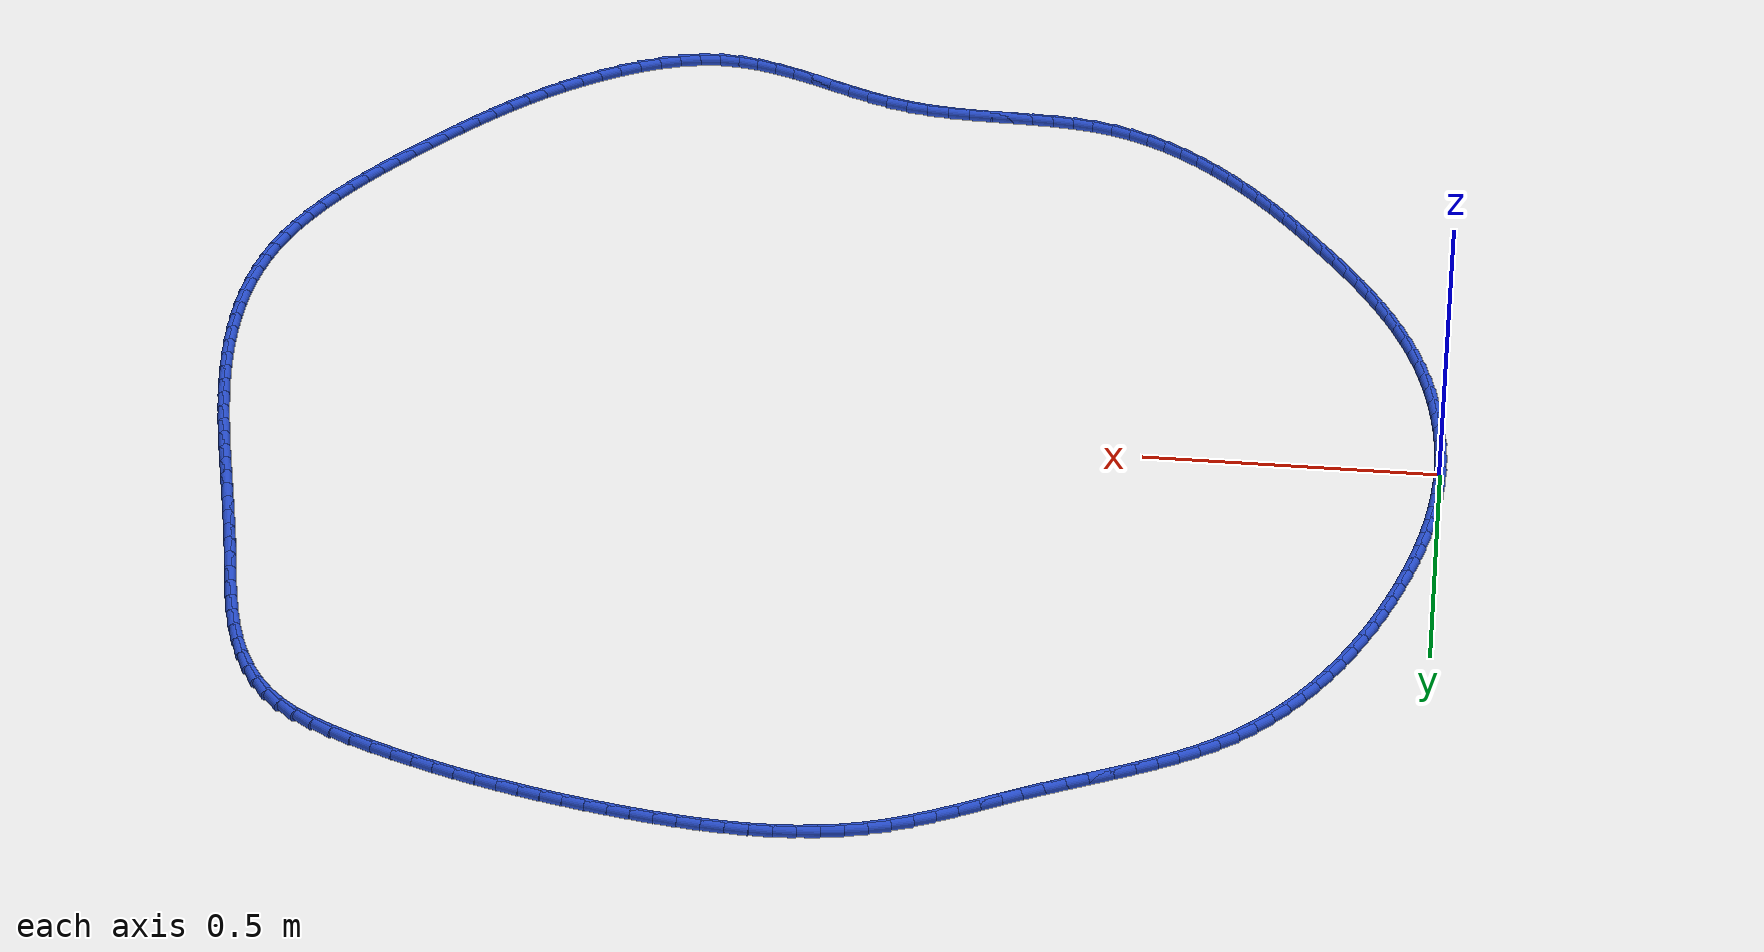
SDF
<sdf version="1.6">
 <world name="default">
  <light name="sun" type="directional">
   <pose>0 0 10 0 -0 0</pose>
   <diffuse>0.8 0.8 0.8 1</diffuse>
   <specular>0.2 0.2 0.2 1</specular>
   <attenuation>
    <range>1000</range>
    <constant>0.9</constant>
    <linear>0.01</linear>
    <quadratic>0.001</quadratic>
   </attenuation>
   <direction>-0.5 0.1 -0.9</direction>
  </light>
  <model name="ground_plane">
   <static>1</static>
   <link name="link">
    <collision name="collision">
     <geometry><plane><normal>0 0 1</normal><size>100 100</size></plane></geometry>
     <surface><friction><ode><mu>100</mu><mu2>50</mu2></ode></friction></surface>
    </collision>
    <visual name="visual">
     <cast_shadows>0</cast_shadows>
     <geometry><plane><normal>0 0 1</normal><size>100 100</size></plane></geometry>
     <material>
      <script><uri>file://media/materials/scripts/gazebo.material</uri><name>Gazebo/WhiteGlow</name></script>
     </material>
    </visual>
   </link>
  </model>
  <gravity>0 0 -9.8</gravity>
  <magnetic_field>6e-06 2.3e-05 -4.2e-05</magnetic_field>
  <atmosphere type="adiabatic"/>
  <physics name="default_physics" default="0" type="ode">
   <max_step_size>0.001</max_step_size>
   <real_time_factor>1</real_time_factor>
   <real_time_update_rate>1000</real_time_update_rate>
  </physics>
  <scene><ambient>0.4 0.4 0.4 1</ambient><background>0.7 0.7 0.7 1</background><shadows>1</shadows></scene>
  <spherical_coordinates>
   <surface_model>EARTH_WGS84</surface_model>
   <latitude_deg>0</latitude_deg>
   <longitude_deg>0</longitude_deg>
   <elevation>0</elevation>
   <heading_deg>0</heading_deg>
  </spherical_coordinates>
  <model name="line">
   <link name="link_0">
    <pose>-2.7755575615628914e-17 -9.71445146547012e-17 0.01 0 1.57 1.542044267432709</pose>
    <collision name="collision">
     <geometry><cylinder><radius>0.01</radius><length>0.08</length></cylinder></geometry>
    </collision>
    <visual name="visual">
     <material>
      <script><name>Gazebo/Blue</name><uri>file://media/materials/scripts/gazebo.material</uri></script>
     </material>
     <geometry><cylinder><radius>0.01</radius><length>0.08</length></cylinder></geometry>
    </visual>
   </link>
   <link name="link_1">
    <pose>0.0010738321835704202 0.03733771721228712 0.01 0 1.57 1.5032818511181816</pose>
    <collision name="collision">
     <geometry><cylinder><radius>0.01</radius><length>0.08</length></cylinder></geometry>
    </collision>
    <visual name="visual">
     <material>
      <script><name>Gazebo/Blue</name><uri>file://media/materials/scripts/gazebo.material</uri></script>
     </material>
     <geometry><cylinder><radius>0.01</radius><length>0.08</length></cylinder></geometry>
    </visual>
   </link>
   <link name="link_2">
    <pose>0.0035869679635209934 0.07450480074108565 0.01 0 1.57 1.4658785739195797</pose>
    <collision name="collision">
     <geometry><cylinder><radius>0.01</radius><length>0.08</length></cylinder></geometry>
    </collision>
    <visual name="visual">
     <material>
      <script><name>Gazebo/Blue</name><uri>file://media/materials/scripts/gazebo.material</uri></script>
     </material>
     <geometry><cylinder><radius>0.01</radius><length>0.08</length></cylinder></geometry>
    </visual>
   </link>
   <link name="link_3">
    <pose>0.007484704561177816 0.11151878774079305 0.01 0 1.57 1.4299813160270398</pose>
    <collision name="collision">
     <geometry><cylinder><radius>0.01</radius><length>0.08</length></cylinder></geometry>
    </collision>
    <visual name="visual">
     <material>
      <script><name>Gazebo/Blue</name><uri>file://media/materials/scripts/gazebo.material</uri></script>
     </material>
     <geometry><cylinder><radius>0.01</radius><length>0.08</length></cylinder></geometry>
    </visual>
   </link>
   <link name="link_4">
    <pose>0.012712339197867031 0.14839721536580708 0.01 0 1.57 1.39570997917218</pose>
    <collision name="collision">
     <geometry><cylinder><radius>0.01</radius><length>0.08</length></cylinder></geometry>
    </collision>
    <visual name="visual">
     <material>
      <script><name>Gazebo/Blue</name><uri>file://media/materials/scripts/gazebo.material</uri></script>
     </material>
     <geometry><cylinder><radius>0.01</radius><length>0.08</length></cylinder></geometry>
    </visual>
   </link>
   <link name="link_5">
    <pose>0.01921516909491475 0.18515762077052528 0.01 0 1.57 1.3631578961786874</pose>
    <collision name="collision">
     <geometry><cylinder><radius>0.01</radius><length>0.08</length></cylinder></geometry>
    </collision>
    <visual name="visual">
     <material>
      <script><name>Gazebo/Blue</name><uri>file://media/materials/scripts/gazebo.material</uri></script>
     </material>
     <geometry><cylinder><radius>0.01</radius><length>0.08</length></cylinder></geometry>
    </visual>
   </link>
   <link name="link_6">
    <pose>0.026938491473647123 0.22181754110934537 0.01 0 1.57 1.332393237809248</pose>
    <collision name="collision">
     <geometry><cylinder><radius>0.01</radius><length>0.08</length></cylinder></geometry>
    </collision>
    <visual name="visual">
     <material>
      <script><name>Gazebo/Blue</name><uri>file://media/materials/scripts/gazebo.material</uri></script>
     </material>
     <geometry><cylinder><radius>0.01</radius><length>0.08</length></cylinder></geometry>
    </visual>
   </link>
   <link name="link_7">
    <pose>0.035827603555390275 0.2583945135366649 0.01 0 1.57 1.3034611595035999</pose>
    <collision name="collision">
     <geometry><cylinder><radius>0.01</radius><length>0.08</length></cylinder></geometry>
    </collision>
    <visual name="visual">
     <material>
      <script><name>Gazebo/Blue</name><uri>file://media/materials/scripts/gazebo.material</uri></script>
     </material>
     <geometry><cylinder><radius>0.01</radius><length>0.08</length></cylinder></geometry>
    </visual>
   </link>
   <link name="link_8">
    <pose>0.04582780256147033 0.29490607520688167 0.01 0 1.57 1.2763864294501093</pose>
    <collision name="collision">
     <geometry><cylinder><radius>0.01</radius><length>0.08</length></cylinder></geometry>
    </collision>
    <visual name="visual">
     <material>
      <script><name>Gazebo/Blue</name><uri>file://media/materials/scripts/gazebo.material</uri></script>
     </material>
     <geometry><cylinder><radius>0.01</radius><length>0.08</length></cylinder></geometry>
    </visual>
   </link>
   <link name="link_9">
    <pose>0.056884385713213415 0.3313697632743931 0.01 0 1.57 1.250950686429554</pose>
    <collision name="collision">
     <geometry><cylinder><radius>0.01</radius><length>0.08</length></cylinder></geometry>
    </collision>
    <visual name="visual">
     <material>
      <script><name>Gazebo/Blue</name><uri>file://media/materials/scripts/gazebo.material</uri></script>
     </material>
     <geometry><cylinder><radius>0.01</radius><length>0.08</length></cylinder></geometry>
    </visual>
   </link>
   <link name="link_10">
    <pose>0.06894845416542092 0.36779309989886144 0.01 0 1.57 1.2248352163170741</pose>
    <collision name="collision">
     <geometry><cylinder><radius>0.01</radius><length>0.08</length></cylinder></geometry>
    </collision>
    <visual name="visual">
     <material>
      <script><name>Gazebo/Blue</name><uri>file://media/materials/scripts/gazebo.material</uri></script>
     </material>
     <geometry><cylinder><radius>0.01</radius><length>0.08</length></cylinder></geometry>
    </visual>
   </link>
   <link name="link_11">
    <pose>0.08202943260990407 0.4040829668865384 0.01 0 1.57 1.1965557212852407</pose>
    <collision name="collision">
     <geometry><cylinder><radius>0.01</radius><length>0.08</length></cylinder></geometry>
    </collision>
    <visual name="visual">
     <material>
      <script><name>Gazebo/Blue</name><uri>file://media/materials/scripts/gazebo.material</uri></script>
     </material>
     <geometry><cylinder><radius>0.01</radius><length>0.08</length></cylinder></geometry>
    </visual>
   </link>
   <link name="link_12">
    <pose>0.0961704415835236 0.4400881020776531 0.01 0 1.57 1.1658818972682463</pose>
    <collision name="collision">
     <geometry><cylinder><radius>0.01</radius><length>0.08</length></cylinder></geometry>
    </collision>
    <visual name="visual">
     <material>
      <script><name>Gazebo/Blue</name><uri>file://media/materials/scripts/gazebo.material</uri></script>
     </material>
     <geometry><cylinder><radius>0.01</radius><length>0.08</length></cylinder></geometry>
    </visual>
   </link>
   <link name="link_13">
    <pose>0.11141501032960267 0.4756565380677785 0.01 0 1.57 1.1325795216238794</pose>
    <collision name="collision">
     <geometry><cylinder><radius>0.01</radius><length>0.08</length></cylinder></geometry>
    </collision>
    <visual name="visual">
     <material>
      <script><name>Gazebo/Blue</name><uri>file://media/materials/scripts/gazebo.material</uri></script>
     </material>
     <geometry><cylinder><radius>0.01</radius><length>0.08</length></cylinder></geometry>
    </visual>
   </link>
   <link name="link_14">
    <pose>0.1278066680914644 0.5106363074524874 0.01 0 1.57 1.0963960438225582</pose>
    <collision name="collision">
     <geometry><cylinder><radius>0.01</radius><length>0.08</length></cylinder></geometry>
    </collision>
    <visual name="visual">
     <material>
      <script><name>Gazebo/Blue</name><uri>file://media/materials/scripts/gazebo.material</uri></script>
     </material>
     <geometry><cylinder><radius>0.01</radius><length>0.08</length></cylinder></geometry>
    </visual>
   </link>
   <link name="link_15">
    <pose>0.14538894411243183 0.5448754428273527 0.01 0 1.57 1.057063886787971</pose>
    <collision name="collision">
     <geometry><cylinder><radius>0.01</radius><length>0.08</length></cylinder></geometry>
    </collision>
    <visual name="visual">
     <material>
      <script><name>Gazebo/Blue</name><uri>file://media/materials/scripts/gazebo.material</uri></script>
     </material>
     <geometry><cylinder><radius>0.01</radius><length>0.08</length></cylinder></geometry>
    </visual>
   </link>
   <link name="link_16">
    <pose>0.1642053676358281 0.578221976787947 0.01 0 1.57 1.0143063775570824</pose>
    <collision name="collision">
     <geometry><cylinder><radius>0.01</radius><length>0.08</length></cylinder></geometry>
    </collision>
    <visual name="visual">
     <material>
      <script><name>Gazebo/Blue</name><uri>file://media/materials/scripts/gazebo.material</uri></script>
     </material>
     <geometry><cylinder><radius>0.01</radius><length>0.08</length></cylinder></geometry>
    </visual>
   </link>
   <link name="link_17">
    <pose>0.1842994679049763 0.610523941929843 0.01 0 1.57 0.9678472984333139</pose>
    <collision name="collision">
     <geometry><cylinder><radius>0.01</radius><length>0.08</length></cylinder></geometry>
    </collision>
    <visual name="visual">
     <material>
      <script><name>Gazebo/Blue</name><uri>file://media/materials/scripts/gazebo.material</uri></script>
     </material>
     <geometry><cylinder><radius>0.01</radius><length>0.08</length></cylinder></geometry>
    </visual>
   </link>
   <link name="link_18">
    <pose>0.20571477416319972 0.641629370848614 0.01 0 1.57 0.9174251667930694</pose>
    <collision name="collision">
     <geometry><cylinder><radius>0.01</radius><length>0.08</length></cylinder></geometry>
    </collision>
    <visual name="visual">
     <material>
      <script><name>Gazebo/Blue</name><uri>file://media/materials/scripts/gazebo.material</uri></script>
     </material>
     <geometry><cylinder><radius>0.01</radius><length>0.08</length></cylinder></geometry>
    </visual>
   </link>
   <link name="link_19">
    <pose>0.22849481565382118 0.6713862961398324 0.01 0 1.57 0.862813296631405</pose>
    <collision name="collision">
     <geometry><cylinder><radius>0.01</radius><length>0.08</length></cylinder></geometry>
    </collision>
    <visual name="visual">
     <material>
      <script><name>Gazebo/Blue</name><uri>file://media/materials/scripts/gazebo.material</uri></script>
     </material>
     <geometry><cylinder><radius>0.01</radius><length>0.08</length></cylinder></geometry>
    </visual>
   </link>
   <link name="link_20">
    <pose>0.25268312162016404 0.699642750399071 0.01 0 1.57 0.8038463039100926</pose>
    <collision name="collision">
     <geometry><cylinder><radius>0.01</radius><length>0.08</length></cylinder></geometry>
    </collision>
    <visual name="visual">
     <material>
      <script><name>Gazebo/Blue</name><uri>file://media/materials/scripts/gazebo.material</uri></script>
     </material>
     <geometry><cylinder><radius>0.01</radius><length>0.08</length></cylinder></geometry>
    </visual>
   </link>
   <link name="link_21">
    <pose>0.2783232213055512 0.7262467662219028 0.01 0 1.57 0.7404527866926917</pose>
    <collision name="collision">
     <geometry><cylinder><radius>0.01</radius><length>0.08</length></cylinder></geometry>
    </collision>
    <visual name="visual">
     <material>
      <script><name>Gazebo/Blue</name><uri>file://media/materials/scripts/gazebo.material</uri></script>
     </material>
     <geometry><cylinder><radius>0.01</radius><length>0.08</length></cylinder></geometry>
    </visual>
   </link>
   <link name="link_22">
    <pose>0.305458643953306 0.7510463762039005 0.01 0 1.57 0.6727658747135454</pose>
    <collision name="collision">
     <geometry><cylinder><radius>0.01</radius><length>0.08</length></cylinder></geometry>
    </collision>
    <visual name="visual">
     <material>
      <script><name>Gazebo/Blue</name><uri>file://media/materials/scripts/gazebo.material</uri></script>
     </material>
     <geometry><cylinder><radius>0.01</radius><length>0.08</length></cylinder></geometry>
    </visual>
   </link>
   <link name="link_23">
    <pose>0.3341315758442072 0.7738919933109771 0.01 0 1.57 0.6062472029265614</pose>
    <collision name="collision">
     <geometry><cylinder><radius>0.01</radius><length>0.08</length></cylinder></geometry>
    </collision>
    <visual name="visual">
     <material>
      <script><name>Gazebo/Blue</name><uri>file://media/materials/scripts/gazebo.material</uri></script>
     </material>
     <geometry><cylinder><radius>0.01</radius><length>0.08</length></cylinder></geometry>
    </visual>
   </link>
   <link name="link_24">
    <pose>0.3642894904764714 0.7948019067460971 0.01 0 1.57 0.5498935238299388</pose>
    <collision name="collision">
     <geometry><cylinder><radius>0.01</radius><length>0.08</length></cylinder></geometry>
    </collision>
    <visual name="visual">
     <material>
      <script><name>Gazebo/Blue</name><uri>file://media/materials/scripts/gazebo.material</uri></script>
     </material>
     <geometry><cylinder><radius>0.01</radius><length>0.08</length></cylinder></geometry>
    </visual>
   </link>
   <link name="link_25">
    <pose>0.3957242946358761 0.8140701441457134 0.01 0 1.57 0.5046655770979783</pose>
    <collision name="collision">
     <geometry><cylinder><radius>0.01</radius><length>0.08</length></cylinder></geometry>
    </collision>
    <visual name="visual">
     <material>
      <script><name>Gazebo/Blue</name><uri>file://media/materials/scripts/gazebo.material</uri></script>
     </material>
     <geometry><cylinder><radius>0.01</radius><length>0.08</length></cylinder></geometry>
    </visual>
   </link>
   <link name="link_26">
    <pose>0.4282134338351014 0.8320163654215093 0.01 0 1.57 0.47042869304620244</pose>
    <collision name="collision">
     <geometry><cylinder><radius>0.01</radius><length>0.08</length></cylinder></geometry>
    </collision>
    <visual name="visual">
     <material>
      <script><name>Gazebo/Blue</name><uri>file://media/materials/scripts/gazebo.material</uri></script>
     </material>
     <geometry><cylinder><radius>0.01</radius><length>0.08</length></cylinder></geometry>
    </visual>
   </link>
   <link name="link_27">
    <pose>0.46153435358682704 0.8489602304851668 0.01 0 1.57 0.4469137473253139</pose>
    <collision name="collision">
     <geometry><cylinder><radius>0.01</radius><length>0.08</length></cylinder></geometry>
    </collision>
    <visual name="visual">
     <material>
      <script><name>Gazebo/Blue</name><uri>file://media/materials/scripts/gazebo.material</uri></script>
     </material>
     <geometry><cylinder><radius>0.01</radius><length>0.08</length></cylinder></geometry>
    </visual>
   </link>
   <link name="link_28">
    <pose>0.49546449940373416 0.8652213992483698 0.01 0 1.57 0.4338386257141746</pose>
    <collision name="collision">
     <geometry><cylinder><radius>0.01</radius><length>0.08</length></cylinder></geometry>
    </collision>
    <visual name="visual">
     <material>
      <script><name>Gazebo/Blue</name><uri>file://media/materials/scripts/gazebo.material</uri></script>
     </material>
     <geometry><cylinder><radius>0.01</radius><length>0.08</length></cylinder></geometry>
    </visual>
   </link>
   <link name="link_29">
    <pose>0.5297813167985025 0.8811195316228012 0.01 0 1.57 0.4309837652098422</pose>
    <collision name="collision">
     <geometry><cylinder><radius>0.01</radius><length>0.08</length></cylinder></geometry>
    </collision>
    <visual name="visual">
     <material>
      <script><name>Gazebo/Blue</name><uri>file://media/materials/scripts/gazebo.material</uri></script>
     </material>
     <geometry><cylinder><radius>0.01</radius><length>0.08</length></cylinder></geometry>
    </visual>
   </link>
   <link name="link_30">
    <pose>0.5642622512838126 0.8969742875201439 0.01 0 1.57 0.4382292288106292</pose>
    <collision name="collision">
     <geometry><cylinder><radius>0.01</radius><length>0.08</length></cylinder></geometry>
    </collision>
    <visual name="visual">
     <material>
      <script><name>Gazebo/Blue</name><uri>file://media/materials/scripts/gazebo.material</uri></script>
     </material>
     <geometry><cylinder><radius>0.01</radius><length>0.08</length></cylinder></geometry>
    </visual>
   </link>
   <link name="link_31">
    <pose>0.5986847483723445 0.9131053268520808 0.01 0 1.57 0.4554360783586779</pose>
    <collision name="collision">
     <geometry><cylinder><radius>0.01</radius><length>0.08</length></cylinder></geometry>
    </collision>
    <visual name="visual">
     <material>
      <script><name>Gazebo/Blue</name><uri>file://media/materials/scripts/gazebo.material</uri></script>
     </material>
     <geometry><cylinder><radius>0.01</radius><length>0.08</length></cylinder></geometry>
    </visual>
   </link>
   <link name="link_32">
    <pose>0.6328283154429344 0.9298280719281702 0.01 0 1.57 0.47427009010933124</pose>
    <collision name="collision">
     <geometry><cylinder><radius>0.01</radius><length>0.08</length></cylinder></geometry>
    </collision>
    <visual name="visual">
     <material>
      <script><name>Gazebo/Blue</name><uri>file://media/materials/scripts/gazebo.material</uri></script>
     </material>
     <geometry><cylinder><radius>0.01</radius><length>0.08</length></cylinder></geometry>
    </visual>
   </link>
   <link name="link_33">
    <pose>0.6666120968548185 0.9471709594245181 0.01 0 1.57 0.48117577384107985</pose>
    <collision name="collision">
     <geometry><cylinder><radius>0.01</radius><length>0.08</length></cylinder></geometry>
    </collision>
    <visual name="visual">
     <material>
      <script><name>Gazebo/Blue</name><uri>file://media/materials/scripts/gazebo.material</uri></script>
     </material>
     <geometry><cylinder><radius>0.01</radius><length>0.08</length></cylinder></geometry>
    </visual>
   </link>
   <link name="link_34">
    <pose>0.7001813645586757 0.9646976825811728 0.01 0 1.57 0.47483751791863194</pose>
    <collision name="collision">
     <geometry><cylinder><radius>0.01</radius><length>0.08</length></cylinder></geometry>
    </collision>
    <visual name="visual">
     <material>
      <script><name>Gazebo/Blue</name><uri>file://media/materials/scripts/gazebo.material</uri></script>
     </material>
     <geometry><cylinder><radius>0.01</radius><length>0.08</length></cylinder></geometry>
    </visual>
   </link>
   <link name="link_35">
    <pose>0.7337020207246079 0.9819295348629115 0.01 0 1.57 0.45503249738478835</pose>
    <collision name="collision">
     <geometry><cylinder><radius>0.01</radius><length>0.08</length></cylinder></geometry>
    </collision>
    <visual name="visual">
     <material>
      <script><name>Gazebo/Blue</name><uri>file://media/materials/scripts/gazebo.material</uri></script>
     </material>
     <geometry><cylinder><radius>0.01</radius><length>0.08</length></cylinder></geometry>
    </visual>
   </link>
   <link name="link_36">
    <pose>0.7673399675227145 0.9983878097345089 0.01 0 1.57 0.4214182944513058</pose>
    <collision name="collision">
     <geometry><cylinder><radius>0.01</radius><length>0.08</length></cylinder></geometry>
    </collision>
    <visual name="visual">
     <material>
      <script><name>Gazebo/Blue</name><uri>file://media/materials/scripts/gazebo.material</uri></script>
     </material>
     <geometry><cylinder><radius>0.01</radius><length>0.08</length></cylinder></geometry>
    </visual>
   </link>
   <link name="link_37">
    <pose>0.8012611071230961 1.013593800660742 0.01 0 1.57 0.3736379798110971</pose>
    <collision name="collision">
     <geometry><cylinder><radius>0.01</radius><length>0.08</length></cylinder></geometry>
    </collision>
    <visual name="visual">
     <material>
      <script><name>Gazebo/Blue</name><uri>file://media/materials/scripts/gazebo.material</uri></script>
     </material>
     <geometry><cylinder><radius>0.01</radius><length>0.08</length></cylinder></geometry>
    </visual>
   </link>
   <link name="link_38">
    <pose>0.8356313416958536 1.027068801106387 0.01 0 1.57 0.31151806013105926</pose>
    <collision name="collision">
     <geometry><cylinder><radius>0.01</radius><length>0.08</length></cylinder></geometry>
    </collision>
    <visual name="visual">
     <material>
      <script><name>Gazebo/Blue</name><uri>file://media/materials/scripts/gazebo.material</uri></script>
     </material>
     <geometry><cylinder><radius>0.01</radius><length>0.08</length></cylinder></geometry>
    </visual>
   </link>
   <link name="link_39">
    <pose>0.8706165675289643 1.0383341189920017 0.01 0 1.57 0.23914272656263086</pose>
    <collision name="collision">
     <geometry><cylinder><radius>0.01</radius><length>0.08</length></cylinder></geometry>
    </collision>
    <visual name="visual">
     <material>
      <script><name>Gazebo/Blue</name><uri>file://media/materials/scripts/gazebo.material</uri></script>
     </material>
     <geometry><cylinder><radius>0.01</radius><length>0.08</length></cylinder></geometry>
    </visual>
   </link>
   <link name="link_40">
    <pose>0.9063296965223263 1.0470412755712806 0.01 0 1.57 0.17013097815499734</pose>
    <collision name="collision">
     <geometry><cylinder><radius>0.01</radius><length>0.08</length></cylinder></geometry>
    </collision>
    <visual name="visual">
     <material>
      <script><name>Gazebo/Blue</name><uri>file://media/materials/scripts/gazebo.material</uri></script>
     </material>
     <geometry><cylinder><radius>0.01</radius><length>0.08</length></cylinder></geometry>
    </visual>
   </link>
   <link name="link_41">
    <pose>0.9427014120818282 1.0532896330649848 0.01 0 1.57 0.10751787181526315</pose>
    <collision name="collision">
     <geometry><cylinder><radius>0.01</radius><length>0.08</length></cylinder></geometry>
    </collision>
    <visual name="visual">
     <material>
      <script><name>Gazebo/Blue</name><uri>file://media/materials/scripts/gazebo.material</uri></script>
     </material>
     <geometry><cylinder><radius>0.01</radius><length>0.08</length></cylinder></geometry>
    </visual>
   </link>
   <link name="link_42">
    <pose>0.9796232513905778 1.0572747586390032 0.01 0 1.57 0.05127410859718429</pose>
    <collision name="collision">
     <geometry><cylinder><radius>0.01</radius><length>0.08</length></cylinder></geometry>
    </collision>
    <visual name="visual">
     <material>
      <script><name>Gazebo/Blue</name><uri>file://media/materials/scripts/gazebo.material</uri></script>
     </material>
     <geometry><cylinder><radius>0.01</radius><length>0.08</length></cylinder></geometry>
    </visual>
   </link>
   <link name="link_43">
    <pose>1.0169867516316833 1.0591922194592238 0.01 0 1.57 0.001203373568329023</pose>
    <collision name="collision">
     <geometry><cylinder><radius>0.01</radius><length>0.08</length></cylinder></geometry>
    </collision>
    <visual name="visual">
     <material>
      <script><name>Gazebo/Blue</name><uri>file://media/materials/scripts/gazebo.material</uri></script>
     </material>
     <geometry><cylinder><radius>0.01</radius><length>0.08</length></cylinder></geometry>
    </visual>
   </link>
   <link name="link_44">
    <pose>1.0546834499882534 1.0592375826915363 0.01 0 1.57 -0.04298788659620403</pose>
    <collision name="collision">
     <geometry><cylinder><radius>0.01</radius><length>0.08</length></cylinder></geometry>
    </collision>
    <visual name="visual">
     <material>
      <script><name>Gazebo/Blue</name><uri>file://media/materials/scripts/gazebo.material</uri></script>
     </material>
     <geometry><cylinder><radius>0.01</radius><length>0.08</length></cylinder></geometry>
    </visual>
   </link>
   <link name="link_45">
    <pose>1.092604883643395 1.0576064155018294 0.01 0 1.57 -0.08163515361936827</pose>
    <collision name="collision">
     <geometry><cylinder><radius>0.01</radius><length>0.08</length></cylinder></geometry>
    </collision>
    <visual name="visual">
     <material>
      <script><name>Gazebo/Blue</name><uri>file://media/materials/scripts/gazebo.material</uri></script>
     </material>
     <geometry><cylinder><radius>0.01</radius><length>0.08</length></cylinder></geometry>
    </visual>
   </link>
   <link name="link_46">
    <pose>1.1306425897802175 1.054494285055992 0.01 0 1.57 -0.11507527590830363</pose>
    <collision name="collision">
     <geometry><cylinder><radius>0.01</radius><length>0.08</length></cylinder></geometry>
    </collision>
    <visual name="visual">
     <material>
      <script><name>Gazebo/Blue</name><uri>file://media/materials/scripts/gazebo.material</uri></script>
     </material>
     <geometry><cylinder><radius>0.01</radius><length>0.08</length></cylinder></geometry>
    </visual>
   </link>
   <link name="link_47">
    <pose>1.1686881055818281 1.0500967585199132 0.01 0 1.57 -0.14361827449836448</pose>
    <collision name="collision">
     <geometry><cylinder><radius>0.01</radius><length>0.08</length></cylinder></geometry>
    </collision>
    <visual name="visual">
     <material>
      <script><name>Gazebo/Blue</name><uri>file://media/materials/scripts/gazebo.material</uri></script>
     </material>
     <geometry><cylinder><radius>0.01</radius><length>0.08</length></cylinder></geometry>
    </visual>
   </link>
   <link name="link_48">
    <pose>1.2066329682313353 1.044609403059481 0.01 0 1.57 -0.16752825161588547</pose>
    <collision name="collision">
     <geometry><cylinder><radius>0.01</radius><length>0.08</length></cylinder></geometry>
    </collision>
    <visual name="visual">
     <material>
      <script><name>Gazebo/Blue</name><uri>file://media/materials/scripts/gazebo.material</uri></script>
     </material>
     <geometry><cylinder><radius>0.01</radius><length>0.08</length></cylinder></geometry>
    </visual>
   </link>
   <link name="link_49">
    <pose>1.2443687149118474 1.038227785840585 0.01 0 1.57 -0.18701559287580305</pose>
    <collision name="collision">
     <geometry><cylinder><radius>0.01</radius><length>0.08</length></cylinder></geometry>
    </collision>
    <visual name="visual">
     <material>
      <script><name>Gazebo/Blue</name><uri>file://media/materials/scripts/gazebo.material</uri></script>
     </material>
     <geometry><cylinder><radius>0.01</radius><length>0.08</length></cylinder></geometry>
    </visual>
   </link>
   <link name="link_50">
    <pose>1.2817870331970609 1.0311472367425183 0.01 0 1.57 -0.20359769543448197</pose>
    <collision name="collision">
     <geometry><cylinder><radius>0.01</radius><length>0.08</length></cylinder></geometry>
    </collision>
    <visual name="visual">
     <material>
      <script><name>Gazebo/Blue</name><uri>file://media/materials/scripts/gazebo.material</uri></script>
     </material>
     <geometry><cylinder><radius>0.01</radius><length>0.08</length></cylinder></geometry>
    </visual>
   </link>
   <link name="link_51">
    <pose>1.3188184587647986 1.023501791021952 0.01 0 1.57 -0.2205141217404757</pose>
    <collision name="collision">
     <geometry><cylinder><radius>0.01</radius><length>0.08</length></cylinder></geometry>
    </collision>
    <visual name="visual">
     <material>
      <script><name>Gazebo/Blue</name><uri>file://media/materials/scripts/gazebo.material</uri></script>
     </material>
     <geometry><cylinder><radius>0.01</radius><length>0.08</length></cylinder></geometry>
    </visual>
   </link>
   <link name="link_52">
    <pose>1.3554839020901341 1.0152828903852007 0.01 0 1.57 -0.23817640800000572</pose>
    <collision name="collision">
     <geometry><cylinder><radius>0.01</radius><length>0.08</length></cylinder></geometry>
    </collision>
    <visual name="visual">
     <material>
      <script><name>Gazebo/Blue</name><uri>file://media/materials/scripts/gazebo.material</uri></script>
     </material>
     <geometry><cylinder><radius>0.01</radius><length>0.08</length></cylinder></geometry>
    </visual>
   </link>
   <link name="link_53">
    <pose>1.3918170966571684 1.006461744367231 0.01 0 1.57 -0.2565286266175927</pose>
    <collision name="collision">
     <geometry><cylinder><radius>0.01</radius><length>0.08</length></cylinder></geometry>
    </collision>
    <visual name="visual">
     <material>
      <script><name>Gazebo/Blue</name><uri>file://media/materials/scripts/gazebo.material</uri></script>
     </material>
     <geometry><cylinder><radius>0.01</radius><length>0.08</length></cylinder></geometry>
    </visual>
   </link>
   <link name="link_54">
    <pose>1.427851775950002 0.997009562503008 0.01 0 1.57 -0.27550698098309806</pose>
    <collision name="collision">
     <geometry><cylinder><radius>0.01</radius><length>0.08</length></cylinder></geometry>
    </collision>
    <visual name="visual">
     <material>
      <script><name>Gazebo/Blue</name><uri>file://media/materials/scripts/gazebo.material</uri></script>
     </material>
     <geometry><cylinder><radius>0.01</radius><length>0.08</length></cylinder></geometry>
    </visual>
   </link>
   <link name="link_55">
    <pose>1.4636216734527376 0.9868975543274977 0.01 0 1.57 -0.29504042134941844</pose>
    <collision name="collision">
     <geometry><cylinder><radius>0.01</radius><length>0.08</length></cylinder></geometry>
    </collision>
    <visual name="visual">
     <material>
      <script><name>Gazebo/Blue</name><uri>file://media/materials/scripts/gazebo.material</uri></script>
     </material>
     <geometry><cylinder><radius>0.01</radius><length>0.08</length></cylinder></geometry>
    </visual>
   </link>
   <link name="link_56">
    <pose>1.4991605226494746 0.9760969293756658 0.01 0 1.57 -0.3150514871713586</pose>
    <collision name="collision">
     <geometry><cylinder><radius>0.01</radius><length>0.08</length></cylinder></geometry>
    </collision>
    <visual name="visual">
     <material>
      <script><name>Gazebo/Blue</name><uri>file://media/materials/scripts/gazebo.material</uri></script>
     </material>
     <geometry><cylinder><radius>0.01</radius><length>0.08</length></cylinder></geometry>
    </visual>
   </link>
   <link name="link_57">
    <pose>1.5345020570243153 0.9645788971824787 0.01 0 1.57 -0.33545736025634537</pose>
    <collision name="collision">
     <geometry><cylinder><radius>0.01</radius><length>0.08</length></cylinder></geometry>
    </collision>
    <visual name="visual">
     <material>
      <script><name>Gazebo/Blue</name><uri>file://media/materials/scripts/gazebo.material</uri></script>
     </material>
     <geometry><cylinder><radius>0.01</radius><length>0.08</length></cylinder></geometry>
    </visual>
   </link>
   <link name="link_58">
    <pose>1.5696800100613608 0.9523146672829016 0.01 0 1.57 -0.3561711002442306</pose>
    <collision name="collision">
     <geometry><cylinder><radius>0.01</radius><length>0.08</length></cylinder></geometry>
    </collision>
    <visual name="visual">
     <material>
      <script><name>Gazebo/Blue</name><uri>file://media/materials/scripts/gazebo.material</uri></script>
     </material>
     <geometry><cylinder><radius>0.01</radius><length>0.08</length></cylinder></geometry>
    </visual>
   </link>
   <link name="link_59">
    <pose>1.604728115244712 0.9392754492119006 0.01 0 1.57 -0.37710302210031255</pose>
    <collision name="collision">
     <geometry><cylinder><radius>0.01</radius><length>0.08</length></cylinder></geometry>
    </collision>
    <visual name="visual">
     <material>
      <script><name>Gazebo/Blue</name><uri>file://media/materials/scripts/gazebo.material</uri></script>
     </material>
     <geometry><cylinder><radius>0.01</radius><length>0.08</length></cylinder></geometry>
    </visual>
   </link>
   <link name="link_60">
    <pose>1.6396801060584705 0.9254324525044416 0.01 0 1.57 -0.3981621656709521</pose>
    <collision name="collision">
     <geometry><cylinder><radius>0.01</radius><length>0.08</length></cylinder></geometry>
    </collision>
    <visual name="visual">
     <material>
      <script><name>Gazebo/Blue</name><uri>file://media/materials/scripts/gazebo.material</uri></script>
     </material>
     <geometry><cylinder><radius>0.01</radius><length>0.08</length></cylinder></geometry>
    </visual>
   </link>
   <link name="link_61">
    <pose>1.6745697159867368 0.9107568866954905 0.01 0 1.57 -0.419648851694626</pose>
    <collision name="collision">
     <geometry><cylinder><radius>0.01</radius><length>0.08</length></cylinder></geometry>
    </collision>
    <visual name="visual">
     <material>
      <script><name>Gazebo/Blue</name><uri>file://media/materials/scripts/gazebo.material</uri></script>
     </material>
     <geometry><cylinder><radius>0.01</radius><length>0.08</length></cylinder></geometry>
    </visual>
   </link>
   <link name="link_62">
    <pose>1.709414326497181 0.8952109136957438 0.01 0 1.57 -0.450964357637427</pose>
    <collision name="collision">
     <geometry><cylinder><radius>0.01</radius><length>0.08</length></cylinder></geometry>
    </collision>
    <visual name="visual">
     <material>
      <script><name>Gazebo/Blue</name><uri>file://media/materials/scripts/gazebo.material</uri></script>
     </material>
     <geometry><cylinder><radius>0.01</radius><length>0.08</length></cylinder></geometry>
    </visual>
   </link>
   <link name="link_63">
    <pose>1.7438402660296033 0.8785403244942891 0.01 0 1.57 -0.5026527869906802</pose>
    <collision name="collision">
     <geometry><cylinder><radius>0.01</radius><length>0.08</length></cylinder></geometry>
    </collision>
    <visual name="visual">
     <material>
      <script><name>Gazebo/Blue</name><uri>file://media/materials/scripts/gazebo.material</uri></script>
     </material>
     <geometry><cylinder><radius>0.01</radius><length>0.08</length></cylinder></geometry>
    </visual>
   </link>
   <link name="link_64">
    <pose>1.77707431572101 0.8602698392484598 0.01 0 1.57 -0.5773322456287442</pose>
    <collision name="collision">
     <geometry><cylinder><radius>0.01</radius><length>0.08</length></cylinder></geometry>
    </collision>
    <visual name="visual">
     <material>
      <script><name>Gazebo/Blue</name><uri>file://media/materials/scripts/gazebo.material</uri></script>
     </material>
     <geometry><cylinder><radius>0.01</radius><length>0.08</length></cylinder></geometry>
    </visual>
   </link>
   <link name="link_65">
    <pose>1.8083252055910648 0.8399141903732167 0.01 0 1.57 -0.6778361975565574</pose>
    <collision name="collision">
     <geometry><cylinder><radius>0.01</radius><length>0.08</length></cylinder></geometry>
    </collision>
    <visual name="visual">
     <material>
      <script><name>Gazebo/Blue</name><uri>file://media/materials/scripts/gazebo.material</uri></script>
     </material>
     <geometry><cylinder><radius>0.01</radius><length>0.08</length></cylinder></geometry>
    </visual>
   </link>
   <link name="link_66">
    <pose>1.8368016656594301 0.8169881102835207 0.01 0 1.57 -0.8023753234262269</pose>
    <collision name="collision">
     <geometry><cylinder><radius>0.01</radius><length>0.08</length></cylinder></geometry>
    </collision>
    <visual name="visual">
     <material>
      <script><name>Gazebo/Blue</name><uri>file://media/materials/scripts/gazebo.material</uri></script>
     </material>
     <geometry><cylinder><radius>0.01</radius><length>0.08</length></cylinder></geometry>
    </visual>
   </link>
   <link name="link_67">
    <pose>1.8618315590400658 0.7910935817719302 0.01 0 1.57 -0.9249435416934194</pose>
    <collision name="collision">
     <geometry><cylinder><radius>0.01</radius><length>0.08</length></cylinder></geometry>
    </collision>
    <visual name="visual">
     <material>
      <script><name>Gazebo/Blue</name><uri>file://media/materials/scripts/gazebo.material</uri></script>
     </material>
     <geometry><cylinder><radius>0.01</radius><length>0.08</length></cylinder></geometry>
    </visual>
   </link>
   <link name="link_68">
    <pose>1.8834787545645817 0.7623716215338526 0.01 0 1.57 -1.033032346026315</pose>
    <collision name="collision">
     <geometry><cylinder><radius>0.01</radius><length>0.08</length></cylinder></geometry>
    </collision>
    <visual name="visual">
     <material>
      <script><name>Gazebo/Blue</name><uri>file://media/materials/scripts/gazebo.material</uri></script>
     </material>
     <geometry><cylinder><radius>0.01</radius><length>0.08</length></cylinder></geometry>
    </visual>
   </link>
   <link name="link_69">
    <pose>1.9020878917542827 0.7311688763529461 0.01 0 1.57 -1.1253564243198841</pose>
    <collision name="collision">
     <geometry><cylinder><radius>0.01</radius><length>0.08</length></cylinder></geometry>
    </collision>
    <visual name="visual">
     <material>
      <script><name>Gazebo/Blue</name><uri>file://media/materials/scripts/gazebo.material</uri></script>
     </material>
     <geometry><cylinder><radius>0.01</radius><length>0.08</length></cylinder></geometry>
    </visual>
   </link>
   <link name="link_70">
    <pose>1.9180041664193725 0.6978324004262481 0.01 0 1.57 -1.2021425630270233</pose>
    <collision name="collision">
     <geometry><cylinder><radius>0.01</radius><length>0.08</length></cylinder></geometry>
    </collision>
    <visual name="visual">
     <material>
      <script><name>Gazebo/Blue</name><uri>file://media/materials/scripts/gazebo.material</uri></script>
     </material>
     <geometry><cylinder><radius>0.01</radius><length>0.08</length></cylinder></geometry>
    </visual>
   </link>
   <link name="link_71">
    <pose>1.9315727743700553 0.6627092479507951 0.01 0 1.57 -1.264420190518695</pose>
    <collision name="collision">
     <geometry><cylinder><radius>0.01</radius><length>0.08</length></cylinder></geometry>
    </collision>
    <visual name="visual">
     <material>
      <script><name>Gazebo/Blue</name><uri>file://media/materials/scripts/gazebo.material</uri></script>
     </material>
     <geometry><cylinder><radius>0.01</radius><length>0.08</length></cylinder></geometry>
    </visual>
   </link>
   <link name="link_72">
    <pose>1.9431389114165358 0.6261464731236253 0.01 0 1.57 -1.313483510984047</pose>
    <collision name="collision">
     <geometry><cylinder><radius>0.01</radius><length>0.08</length></cylinder></geometry>
    </collision>
    <visual name="visual">
     <material>
      <script><name>Gazebo/Blue</name><uri>file://media/materials/scripts/gazebo.material</uri></script>
     </material>
     <geometry><cylinder><radius>0.01</radius><length>0.08</length></cylinder></geometry>
    </visual>
   </link>
   <link name="link_73">
    <pose>1.9530477733690177 0.5884911301417752 0.01 0 1.57 -1.3505581205387494</pose>
    <collision name="collision">
     <geometry><cylinder><radius>0.01</radius><length>0.08</length></cylinder></geometry>
    </collision>
    <visual name="visual">
     <material>
      <script><name>Gazebo/Blue</name><uri>file://media/materials/scripts/gazebo.material</uri></script>
     </material>
     <geometry><cylinder><radius>0.01</radius><length>0.08</length></cylinder></geometry>
    </visual>
   </link>
   <link name="link_74">
    <pose>1.9616445560377045 0.5500902732022815 0.01 0 1.57 -1.3766236495050503</pose>
    <collision name="collision">
     <geometry><cylinder><radius>0.01</radius><length>0.08</length></cylinder></geometry>
    </collision>
    <visual name="visual">
     <material>
      <script><name>Gazebo/Blue</name><uri>file://media/materials/scripts/gazebo.material</uri></script>
     </material>
     <geometry><cylinder><radius>0.01</radius><length>0.08</length></cylinder></geometry>
    </visual>
   </link>
   <link name="link_75">
    <pose>1.9692744552328019 0.5112909565021825 0.01 0 1.57 -1.3923274051119814</pose>
    <collision name="collision">
     <geometry><cylinder><radius>0.01</radius><length>0.08</length></cylinder></geometry>
    </collision>
    <visual name="visual">
     <material>
      <script><name>Gazebo/Blue</name><uri>file://media/materials/scripts/gazebo.material</uri></script>
     </material>
     <geometry><cylinder><radius>0.01</radius><length>0.08</length></cylinder></geometry>
    </visual>
   </link>
   <link name="link_76">
    <pose>1.9762826667645124 0.47244023423851444 0.01 0 1.57 -1.3979387044781846</pose>
    <collision name="collision">
     <geometry><cylinder><radius>0.01</radius><length>0.08</length></cylinder></geometry>
    </collision>
    <visual name="visual">
     <material>
      <script><name>Gazebo/Blue</name><uri>file://media/materials/scripts/gazebo.material</uri></script>
     </material>
     <geometry><cylinder><radius>0.01</radius><length>0.08</length></cylinder></geometry>
    </visual>
   </link>
   <link name="link_77">
    <pose>1.9830143864430414 0.43388516060831445 0.01 0 1.57 -1.3935712095662527</pose>
    <collision name="collision">
     <geometry><cylinder><radius>0.01</radius><length>0.08</length></cylinder></geometry>
    </collision>
    <visual name="visual">
     <material>
      <script><name>Gazebo/Blue</name><uri>file://media/materials/scripts/gazebo.material</uri></script>
     </material>
     <geometry><cylinder><radius>0.01</radius><length>0.08</length></cylinder></geometry>
    </visual>
   </link>
   <link name="link_78">
    <pose>1.9898066831479977 0.3959614454997415 0.01 0 1.57 -1.3848058987437937</pose>
    <collision name="collision">
     <geometry><cylinder><radius>0.01</radius><length>0.08</length></cylinder></geometry>
    </collision>
    <visual name="visual">
     <material>
      <script><name>Gazebo/Blue</name><uri>file://media/materials/scripts/gazebo.material</uri></script>
     </material>
     <geometry><cylinder><radius>0.01</radius><length>0.08</length></cylinder></geometry>
    </visual>
   </link>
   <link name="link_79">
    <pose>1.996809726529554 0.3587439078577616 0.01 0 1.57 -1.3776598432863572</pose>
    <collision name="collision">
     <geometry><cylinder><radius>0.01</radius><length>0.08</length></cylinder></geometry>
    </collision>
    <visual name="visual">
     <material>
      <script><name>Gazebo/Blue</name><uri>file://media/materials/scripts/gazebo.material</uri></script>
     </material>
     <geometry><cylinder><radius>0.01</radius><length>0.08</length></cylinder></geometry>
    </visual>
   </link>
   <link name="link_80">
    <pose>2.003986798215658 0.3220464913281987 0.01 0 1.57 -1.372573026748038</pose>
    <collision name="collision">
     <geometry><cylinder><radius>0.01</radius><length>0.08</length></cylinder></geometry>
    </collision>
    <visual name="visual">
     <material>
      <script><name>Gazebo/Blue</name><uri>file://media/materials/scripts/gazebo.material</uri></script>
     </material>
     <geometry><cylinder><radius>0.01</radius><length>0.08</length></cylinder></geometry>
    </visual>
   </link>
   <link name="link_81">
    <pose>2.011293055145107 0.2856717983768093 0.01 0 1.57 -1.3696707258092908</pose>
    <collision name="collision">
     <geometry><cylinder><radius>0.01</radius><length>0.08</length></cylinder></geometry>
    </collision>
    <visual name="visual">
     <material>
      <script><name>Gazebo/Blue</name><uri>file://media/materials/scripts/gazebo.material</uri></script>
     </material>
     <geometry><cylinder><radius>0.01</radius><length>0.08</length></cylinder></geometry>
    </visual>
   </link>
   <link name="link_82">
    <pose>2.018683654256698 0.2494224314693489 0.01 0 1.57 -1.3690151377993818</pose>
    <collision name="collision">
     <geometry><cylinder><radius>0.01</radius><length>0.08</length></cylinder></geometry>
    </collision>
    <visual name="visual">
     <material>
      <script><name>Gazebo/Blue</name><uri>file://media/materials/scripts/gazebo.material</uri></script>
     </material>
     <geometry><cylinder><radius>0.01</radius><length>0.08</length></cylinder></geometry>
    </visual>
   </link>
   <link name="link_83">
    <pose>2.0261137524892283 0.2131009930715731 0.01 0 1.57 -1.3706018141863443</pose>
    <collision name="collision">
     <geometry><cylinder><radius>0.01</radius><length>0.08</length></cylinder></geometry>
    </collision>
    <visual name="visual">
     <material>
      <script><name>Gazebo/Blue</name><uri>file://media/materials/scripts/gazebo.material</uri></script>
     </material>
     <geometry><cylinder><radius>0.01</radius><length>0.08</length></cylinder></geometry>
    </visual>
   </link>
   <link name="link_84">
    <pose>2.0335385067785423 0.17651008565923454 0.01 0 1.57 -1.3744735034587647</pose>
    <collision name="collision">
     <geometry><cylinder><radius>0.01</radius><length>0.08</length></cylinder></geometry>
    </collision>
    <visual name="visual">
     <material>
      <script><name>Gazebo/Blue</name><uri>file://media/materials/scripts/gazebo.material</uri></script>
     </material>
     <geometry><cylinder><radius>0.01</radius><length>0.08</length></cylinder></geometry>
    </visual>
   </link>
   <link name="link_85">
    <pose>2.0408997732736074 0.13949733174236656 0.01 0 1.57 -1.380985036129335</pose>
    <collision name="collision">
     <geometry><cylinder><radius>0.01</radius><length>0.08</length></cylinder></geometry>
    </collision>
    <visual name="visual">
     <material>
      <script><name>Gazebo/Blue</name><uri>file://media/materials/scripts/gazebo.material</uri></script>
     </material>
     <geometry><cylinder><radius>0.01</radius><length>0.08</length></cylinder></geometry>
    </visual>
   </link>
   <link name="link_86">
    <pose>2.048087168485579 0.10208717271451374 0.01 0 1.57 -1.3902106341222915</pose>
    <collision name="collision">
     <geometry><cylinder><radius>0.01</radius><length>0.08</length></cylinder></geometry>
    </collision>
    <visual name="visual">
     <material>
      <script><name>Gazebo/Blue</name><uri>file://media/materials/scripts/gazebo.material</uri></script>
     </material>
     <geometry><cylinder><radius>0.01</radius><length>0.08</length></cylinder></geometry>
    </visual>
   </link>
   <link name="link_87">
    <pose>2.0549774855470124 0.06434745408880159 0.01 0 1.57 -1.402155833394586</pose>
    <collision name="collision">
     <geometry><cylinder><radius>0.01</radius><length>0.08</length></cylinder></geometry>
    </collision>
    <visual name="visual">
     <material>
      <script><name>Gazebo/Blue</name><uri>file://media/materials/scripts/gazebo.material</uri></script>
     </material>
     <geometry><cylinder><radius>0.01</radius><length>0.08</length></cylinder></geometry>
    </visual>
   </link>
   <link name="link_88">
    <pose>2.061447517590466 0.026346021378355677 0.01 0 1.57 -1.4168597650586177</pose>
    <collision name="collision">
     <geometry><cylinder><radius>0.01</radius><length>0.08</length></cylinder></geometry>
    </collision>
    <visual name="visual">
     <material>
      <script><name>Gazebo/Blue</name><uri>file://media/materials/scripts/gazebo.material</uri></script>
     </material>
     <geometry><cylinder><radius>0.01</radius><length>0.08</length></cylinder></geometry>
    </visual>
   </link>
   <link name="link_89">
    <pose>2.067374057748495 -0.01184927990369731 0.01 0 1.57 -1.434392395922009</pose>
    <collision name="collision">
     <geometry><cylinder><radius>0.01</radius><length>0.08</length></cylinder></geometry>
    </collision>
    <visual name="visual">
     <material>
      <script><name>Gazebo/Blue</name><uri>file://media/materials/scripts/gazebo.material</uri></script>
     </material>
     <geometry><cylinder><radius>0.01</radius><length>0.08</length></cylinder></geometry>
    </visual>
   </link>
   <link name="link_90">
    <pose>2.0726338991536557 -0.05017060424423188 0.01 0 1.57 -1.4548519382766725</pose>
    <collision name="collision">
     <geometry><cylinder><radius>0.01</radius><length>0.08</length></cylinder></geometry>
    </collision>
    <visual name="visual">
     <material>
      <script><name>Gazebo/Blue</name><uri>file://media/materials/scripts/gazebo.material</uri></script>
     </material>
     <geometry><cylinder><radius>0.01</radius><length>0.08</length></cylinder></geometry>
    </visual>
   </link>
   <link name="link_91">
    <pose>2.0771038349385047 -0.08855010613012214 0.01 0 1.57 -1.478362057065576</pose>
    <collision name="collision">
     <geometry><cylinder><radius>0.01</radius><length>0.08</length></cylinder></geometry>
    </collision>
    <visual name="visual">
     <material>
      <script><name>Gazebo/Blue</name><uri>file://media/materials/scripts/gazebo.material</uri></script>
     </material>
     <geometry><cylinder><radius>0.01</radius><length>0.08</length></cylinder></geometry>
    </visual>
   </link>
   <link name="link_92">
    <pose>2.0806606582355993 -0.12691994004824284 0.01 0 1.57 -1.5050684416330349</pose>
    <collision name="collision">
     <geometry><cylinder><radius>0.01</radius><length>0.08</length></cylinder></geometry>
    </collision>
    <visual name="visual">
     <material>
      <script><name>Gazebo/Blue</name><uri>file://media/materials/scripts/gazebo.material</uri></script>
     </material>
     <geometry><cylinder><radius>0.01</radius><length>0.08</length></cylinder></geometry>
    </visual>
   </link>
   <link name="link_93">
    <pose>2.083181162177495 -0.16521226048546656 0.01 0 1.57 -1.5351342278567448</pose>
    <collision name="collision">
     <geometry><cylinder><radius>0.01</radius><length>0.08</length></cylinder></geometry>
    </collision>
    <visual name="visual">
     <material>
      <script><name>Gazebo/Blue</name><uri>file://media/materials/scripts/gazebo.material</uri></script>
     </material>
     <geometry><cylinder><radius>0.01</radius><length>0.08</length></cylinder></geometry>
    </visual>
   </link>
   <link name="link_94">
    <pose>2.0845421398967487 -0.2033592219286682 0.01 0 1.57 -1.5687336648145733</pose>
    <collision name="collision">
     <geometry><cylinder><radius>0.01</radius><length>0.08</length></cylinder></geometry>
    </collision>
    <visual name="visual">
     <material>
      <script><name>Gazebo/Blue</name><uri>file://media/materials/scripts/gazebo.material</uri></script>
     </material>
     <geometry><cylinder><radius>0.01</radius><length>0.08</length></cylinder></geometry>
    </visual>
   </link>
   <link name="link_95">
    <pose>2.0846203845259175 -0.24129297886472192 0.01 0 1.57 1.5355493135015228</pose>
    <collision name="collision">
     <geometry><cylinder><radius>0.01</radius><length>0.08</length></cylinder></geometry>
    </collision>
    <visual name="visual">
     <material>
      <script><name>Gazebo/Blue</name><uri>file://media/materials/scripts/gazebo.material</uri></script>
     </material>
     <geometry><cylinder><radius>0.01</radius><length>0.08</length></cylinder></geometry>
    </visual>
   </link>
   <link name="link_96">
    <pose>2.083292689197557 -0.2789456857805016 0.01 0 1.57 1.4943624044121893</pose>
    <collision name="collision">
     <geometry><cylinder><radius>0.01</radius><length>0.08</length></cylinder></geometry>
    </collision>
    <visual name="visual">
     <material>
      <script><name>Gazebo/Blue</name><uri>file://media/materials/scripts/gazebo.material</uri></script>
     </material>
     <geometry><cylinder><radius>0.01</radius><length>0.08</length></cylinder></geometry>
    </visual>
   </link>
   <link name="link_97">
    <pose>2.080435847044224 -0.31624949716288153 0.01 0 1.57 1.4491565723511608</pose>
    <collision name="collision">
     <geometry><cylinder><radius>0.01</radius><length>0.08</length></cylinder></geometry>
    </collision>
    <visual name="visual">
     <material>
      <script><name>Gazebo/Blue</name><uri>file://media/materials/scripts/gazebo.material</uri></script>
     </material>
     <geometry><cylinder><radius>0.01</radius><length>0.08</length></cylinder></geometry>
    </visual>
   </link>
   <link name="link_98">
    <pose>2.0759266511984746 -0.3531365674987364 0.01 0 1.57 1.3998352687338307</pose>
    <collision name="collision">
     <geometry><cylinder><radius>0.01</radius><length>0.08</length></cylinder></geometry>
    </collision>
    <visual name="visual">
     <material>
      <script><name>Gazebo/Blue</name><uri>file://media/materials/scripts/gazebo.material</uri></script>
     </material>
     <geometry><cylinder><radius>0.01</radius><length>0.08</length></cylinder></geometry>
    </visual>
   </link>
   <link name="link_99">
    <pose>2.0696418947928663 -0.3895390512749388 0.01 0 1.57 1.3463707770386413</pose>
    <collision name="collision">
     <geometry><cylinder><radius>0.01</radius><length>0.08</length></cylinder></geometry>
    </collision>
    <visual name="visual">
     <material>
      <script><name>Gazebo/Blue</name><uri>file://media/materials/scripts/gazebo.material</uri></script>
     </material>
     <geometry><cylinder><radius>0.01</radius><length>0.08</length></cylinder></geometry>
    </visual>
   </link>
   <link name="link_100">
    <pose>2.061458370959955 -0.42538910297836374 0.01 0 1.57 1.2888305138795781</pose>
    <collision name="collision">
     <geometry><cylinder><radius>0.01</radius><length>0.08</length></cylinder></geometry>
    </collision>
    <visual name="visual">
     <material>
      <script><name>Gazebo/Blue</name><uri>file://media/materials/scripts/gazebo.material</uri></script>
     </material>
     <geometry><cylinder><radius>0.01</radius><length>0.08</length></cylinder></geometry>
    </visual>
   </link>
   <link name="link_101">
    <pose>2.0512528728322974 -0.46061887709588517 0.01 0 1.57 1.2274576967214703</pose>
    <collision name="collision">
     <geometry><cylinder><radius>0.01</radius><length>0.08</length></cylinder></geometry>
    </collision>
    <visual name="visual">
     <material>
      <script><name>Gazebo/Blue</name><uri>file://media/materials/scripts/gazebo.material</uri></script>
     </material>
     <geometry><cylinder><radius>0.01</radius><length>0.08</length></cylinder></geometry>
    </visual>
   </link>
   <link name="link_102">
    <pose>2.0389041055292685 -0.4951611032866791 0.01 0 1.57 1.165954389898391</pose>
    <collision name="collision">
     <geometry><cylinder><radius>0.01</radius><length>0.08</length></cylinder></geometry>
    </collision>
    <visual name="visual">
     <material>
      <script><name>Gazebo/Blue</name><uri>file://media/materials/scripts/gazebo.material</uri></script>
     </material>
     <geometry><cylinder><radius>0.01</radius><length>0.08</length></cylinder></geometry>
    </visual>
   </link>
   <link name="link_103">
    <pose>2.0244103653101533 -0.528984487143718 0.01 0 1.57 1.1098748235185218</pose>
    <collision name="collision">
     <geometry><cylinder><radius>0.01</radius><length>0.08</length></cylinder></geometry>
    </collision>
    <visual name="visual">
     <material>
      <script><name>Gazebo/Blue</name><uri>file://media/materials/scripts/gazebo.material</uri></script>
     </material>
     <geometry><cylinder><radius>0.01</radius><length>0.08</length></cylinder></geometry>
    </visual>
   </link>
   <link name="link_104">
    <pose>2.007958171692154 -0.562114356409999 0.01 0 1.57 1.0596922271778646</pose>
    <collision name="collision">
     <geometry><cylinder><radius>0.01</radius><length>0.08</length></cylinder></geometry>
    </collision>
    <visual name="visual">
     <material>
      <script><name>Gazebo/Blue</name><uri>file://media/materials/scripts/gazebo.material</uri></script>
     </material>
     <geometry><cylinder><radius>0.01</radius><length>0.08</length></cylinder></geometry>
    </visual>
   </link>
   <link name="link_105">
    <pose>1.9897505740231898 -0.5945810114050507 0.01 0 1.57 1.0152781321937727</pose>
    <collision name="collision">
     <geometry><cylinder><radius>0.01</radius><length>0.08</length></cylinder></geometry>
    </collision>
    <visual name="visual">
     <material>
      <script><name>Gazebo/Blue</name><uri>file://media/materials/scripts/gazebo.material</uri></script>
     </material>
     <geometry><cylinder><radius>0.01</radius><length>0.08</length></cylinder></geometry>
    </visual>
   </link>
   <link name="link_106">
    <pose>1.9699906216511787 -0.6264147524484014 0.01 0 1.57 0.976425578339522</pose>
    <collision name="collision">
     <geometry><cylinder><radius>0.01</radius><length>0.08</length></cylinder></geometry>
    </collision>
    <visual name="visual">
     <material>
      <script><name>Gazebo/Blue</name><uri>file://media/materials/scripts/gazebo.material</uri></script>
     </material>
     <geometry><cylinder><radius>0.01</radius><length>0.08</length></cylinder></geometry>
    </visual>
   </link>
   <link name="link_107">
    <pose>1.9488813639240374 -0.6576458798595787 0.01 0 1.57 0.9428924711230825</pose>
    <collision name="collision">
     <geometry><cylinder><radius>0.01</radius><length>0.08</length></cylinder></geometry>
    </collision>
    <visual name="visual">
     <material>
      <script><name>Gazebo/Blue</name><uri>file://media/materials/scripts/gazebo.material</uri></script>
     </material>
     <geometry><cylinder><radius>0.01</radius><length>0.08</length></cylinder></geometry>
    </visual>
   </link>
   <link name="link_108">
    <pose>1.9266258501896838 -0.6883046939581104 0.01 0 1.57 0.9144345413566514</pose>
    <collision name="collision">
     <geometry><cylinder><radius>0.01</radius><length>0.08</length></cylinder></geometry>
    </collision>
    <visual name="visual">
     <material>
      <script><name>Gazebo/Blue</name><uri>file://media/materials/scripts/gazebo.material</uri></script>
     </material>
     <geometry><cylinder><radius>0.01</radius><length>0.08</length></cylinder></geometry>
    </visual>
   </link>
   <link name="link_109">
    <pose>1.9034271297960357 -0.7184214950635255 0.01 0 1.57 0.8908292863738507</pose>
    <collision name="collision">
     <geometry><cylinder><radius>0.01</radius><length>0.08</length></cylinder></geometry>
    </collision>
    <visual name="visual">
     <material>
      <script><name>Gazebo/Blue</name><uri>file://media/materials/scripts/gazebo.material</uri></script>
     </material>
     <geometry><cylinder><radius>0.01</radius><length>0.08</length></cylinder></geometry>
    </visual>
   </link>
   <link name="link_110">
    <pose>1.879488252091011 -0.74802658349535 0.01 0 1.57 0.8718930055013202</pose>
    <collision name="collision">
     <geometry><cylinder><radius>0.01</radius><length>0.08</length></cylinder></geometry>
    </collision>
    <visual name="visual">
     <material>
      <script><name>Gazebo/Blue</name><uri>file://media/materials/scripts/gazebo.material</uri></script>
     </material>
     <geometry><cylinder><radius>0.01</radius><length>0.08</length></cylinder></geometry>
    </visual>
   </link>
   <link name="link_111">
    <pose>1.855012266422527 -0.7771502595731128 0.01 0 1.57 0.8574931025229686</pose>
    <collision name="collision">
     <geometry><cylinder><radius>0.01</radius><length>0.08</length></cylinder></geometry>
    </collision>
    <visual name="visual">
     <material>
      <script><name>Gazebo/Blue</name><uri>file://media/materials/scripts/gazebo.material</uri></script>
     </material>
     <geometry><cylinder><radius>0.01</radius><length>0.08</length></cylinder></geometry>
    </visual>
   </link>
   <link name="link_112">
    <pose>1.8302022221385017 -0.8058228236163416 0.01 0 1.57 0.8464655483616461</pose>
    <collision name="collision">
     <geometry><cylinder><radius>0.01</radius><length>0.08</length></cylinder></geometry>
    </collision>
    <visual name="visual">
     <material>
      <script><name>Gazebo/Blue</name><uri>file://media/materials/scripts/gazebo.material</uri></script>
     </material>
     <geometry><cylinder><radius>0.01</radius><length>0.08</length></cylinder></geometry>
    </visual>
   </link>
   <link name="link_113">
    <pose>1.8052184232487718 -0.8340607822312759 0.01 0 1.57 0.8329936706009642</pose>
    <collision name="collision">
     <geometry><cylinder><radius>0.01</radius><length>0.08</length></cylinder></geometry>
    </collision>
    <visual name="visual">
     <material>
      <script><name>Gazebo/Blue</name><uri>file://media/materials/scripts/gazebo.material</uri></script>
     </material>
     <geometry><cylinder><radius>0.01</radius><length>0.08</length></cylinder></geometry>
    </visual>
   </link>
   <link name="link_114">
    <pose>1.779994706484051 -0.8618075621315199 0.01 0 1.57 0.815143465448513</pose>
    <collision name="collision">
     <geometry><cylinder><radius>0.01</radius><length>0.08</length></cylinder></geometry>
    </collision>
    <visual name="visual">
     <material>
      <script><name>Gazebo/Blue</name><uri>file://media/materials/scripts/gazebo.material</uri></script>
     </material>
     <geometry><cylinder><radius>0.01</radius><length>0.08</length></cylinder></geometry>
    </visual>
   </link>
   <link name="link_115">
    <pose>1.754390192433558 -0.8889824794941837 0.01 0 1.57 0.7929218471101661</pose>
    <collision name="collision">
     <geometry><cylinder><radius>0.01</radius><length>0.08</length></cylinder></geometry>
    </collision>
    <visual name="visual">
     <material>
      <script><name>Gazebo/Blue</name><uri>file://media/materials/scripts/gazebo.material</uri></script>
     </material>
     <geometry><cylinder><radius>0.01</radius><length>0.08</length></cylinder></geometry>
    </visual>
   </link>
   <link name="link_116">
    <pose>1.7282639552527157 -0.9155048355124138 0.01 0 1.57 0.7663850751509137</pose>
    <collision name="collision">
     <geometry><cylinder><radius>0.01</radius><length>0.08</length></cylinder></geometry>
    </collision>
    <visual name="visual">
     <material>
      <script><name>Gazebo/Blue</name><uri>file://media/materials/scripts/gazebo.material</uri></script>
     </material>
     <geometry><cylinder><radius>0.01</radius><length>0.08</length></cylinder></geometry>
    </visual>
   </link>
   <link name="link_117">
    <pose>1.7014750690969411 -0.9412939313793574 0.01 0 1.57 0.7356495617890833</pose>
    <collision name="collision">
     <geometry><cylinder><radius>0.01</radius><length>0.08</length></cylinder></geometry>
    </collision>
    <visual name="visual">
     <material>
      <script><name>Gazebo/Blue</name><uri>file://media/materials/scripts/gazebo.material</uri></script>
     </material>
     <geometry><cylinder><radius>0.01</radius><length>0.08</length></cylinder></geometry>
    </visual>
   </link>
   <link name="link_118">
    <pose>1.673882608121655 -0.9662690682881614 0.01 0 1.57 0.7009038965185695</pose>
    <collision name="collision">
     <geometry><cylinder><radius>0.01</radius><length>0.08</length></cylinder></geometry>
    </collision>
    <visual name="visual">
     <material>
      <script><name>Gazebo/Blue</name><uri>file://media/materials/scripts/gazebo.material</uri></script>
     </material>
     <geometry><cylinder><radius>0.01</radius><length>0.08</length></cylinder></geometry>
    </visual>
   </link>
   <link name="link_119">
    <pose>1.6453456464822762 -0.9903495474319735 0.01 0 1.57 0.6624191537782965</pose>
    <collision name="collision">
     <geometry><cylinder><radius>0.01</radius><length>0.08</length></cylinder></geometry>
    </collision>
    <visual name="visual">
     <material>
      <script><name>Gazebo/Blue</name><uri>file://media/materials/scripts/gazebo.material</uri></script>
     </material>
     <geometry><cylinder><radius>0.01</radius><length>0.08</length></cylinder></geometry>
    </visual>
   </link>
   <link name="link_120">
    <pose>1.615723258334224 -1.0134546700039406 0.01 0 1.57 0.6205553473145585</pose>
    <collision name="collision">
     <geometry><cylinder><radius>0.01</radius><length>0.08</length></cylinder></geometry>
    </collision>
    <visual name="visual">
     <material>
      <script><name>Gazebo/Blue</name><uri>file://media/materials/scripts/gazebo.material</uri></script>
     </material>
     <geometry><cylinder><radius>0.01</radius><length>0.08</length></cylinder></geometry>
    </visual>
   </link>
   <link name="link_121">
    <pose>1.5848745178329187 -1.0355037371972091 0.01 0 1.57 0.5757426898340138</pose>
    <collision name="collision">
     <geometry><cylinder><radius>0.01</radius><length>0.08</length></cylinder></geometry>
    </collision>
    <visual name="visual">
     <material>
      <script><name>Gazebo/Blue</name><uri>file://media/materials/scripts/gazebo.material</uri></script>
     </material>
     <geometry><cylinder><radius>0.01</radius><length>0.08</length></cylinder></geometry>
    </visual>
   </link>
   <link name="link_122">
    <pose>1.552659866821432 -1.0564142863256576 0.01 0 1.57 0.5262530416023268</pose>
    <collision name="collision">
     <geometry><cylinder><radius>0.01</radius><length>0.08</length></cylinder></geometry>
    </collision>
    <visual name="visual">
     <material>
      <script><name>Gazebo/Blue</name><uri>file://media/materials/scripts/gazebo.material</uri></script>
     </material>
     <geometry><cylinder><radius>0.01</radius><length>0.08</length></cylinder></geometry>
    </visual>
   </link>
   <link name="link_123">
    <pose>1.519083272358157 -1.0759187531185377 0.01 0 1.57 0.4671531648743144</pose>
    <collision name="collision">
     <geometry><cylinder><radius>0.01</radius><length>0.08</length></cylinder></geometry>
    </collision>
    <visual name="visual">
     <material>
      <script><name>Gazebo/Blue</name><uri>file://media/materials/scripts/gazebo.material</uri></script>
     </material>
     <geometry><cylinder><radius>0.01</radius><length>0.08</length></cylinder></geometry>
    </visual>
   </link>
   <link name="link_124">
    <pose>1.4844163528327043 -1.0934043887643528 0.01 0 1.57 0.39582009256335854</pose>
    <collision name="collision">
     <geometry><cylinder><radius>0.01</radius><length>0.08</length></cylinder></geometry>
    </collision>
    <visual name="visual">
     <material>
      <script><name>Gazebo/Blue</name><uri>file://media/materials/scripts/gazebo.material</uri></script>
     </material>
     <geometry><cylinder><radius>0.01</radius><length>0.08</length></cylinder></geometry>
    </visual>
   </link>
   <link name="link_125">
    <pose>1.4489599840577492 -1.1082207117412972 0.01 0 1.57 0.30955523743675306</pose>
    <collision name="collision">
     <geometry><cylinder><radius>0.01</radius><length>0.08</length></cylinder></geometry>
    </collision>
    <visual name="visual">
     <material>
      <script><name>Gazebo/Blue</name><uri>file://media/materials/scripts/gazebo.material</uri></script>
     </material>
     <geometry><cylinder><radius>0.01</radius><length>0.08</length></cylinder></geometry>
    </visual>
   </link>
   <link name="link_126">
    <pose>1.4130150418459682 -1.1197172405275682 0.01 0 1.57 0.20535877902911692</pose>
    <collision name="collision">
     <geometry><cylinder><radius>0.01</radius><length>0.08</length></cylinder></geometry>
    </collision>
    <visual name="visual">
     <material>
      <script><name>Gazebo/Blue</name><uri>file://media/materials/scripts/gazebo.material</uri></script>
     </material>
     <geometry><cylinder><radius>0.01</radius><length>0.08</length></cylinder></geometry>
    </visual>
   </link>
   <link name="link_127">
    <pose>1.3768824020100376 -1.1272434936013593 0.01 0 1.57 0.08049033464202657</pose>
    <collision name="collision">
     <geometry><cylinder><radius>0.01</radius><length>0.08</length></cylinder></geometry>
    </collision>
    <visual name="visual">
     <material>
      <script><name>Gazebo/Blue</name><uri>file://media/materials/scripts/gazebo.material</uri></script>
     </material>
     <geometry><cylinder><radius>0.01</radius><length>0.08</length></cylinder></geometry>
    </visual>
   </link>
   <link name="link_128">
    <pose>1.3408629403626335 -1.1301489894408672 0.01 0 1.57 -0.05976134134294635</pose>
    <collision name="collision">
     <geometry><cylinder><radius>0.01</radius><length>0.08</length></cylinder></geometry>
    </collision>
    <visual name="visual">
     <material>
      <script><name>Gazebo/Blue</name><uri>file://media/materials/scripts/gazebo.material</uri></script>
     </material>
     <geometry><cylinder><radius>0.01</radius><length>0.08</length></cylinder></geometry>
    </visual>
   </link>
   <link name="link_129">
    <pose>1.3051957104190524 -1.128014926789158 0.01 0 1.57 -0.18412007941442937</pose>
    <collision name="collision">
     <geometry><cylinder><radius>0.01</radius><length>0.08</length></cylinder></geometry>
    </collision>
    <visual name="visual">
     <material>
      <script><name>Gazebo/Blue</name><uri>file://media/materials/scripts/gazebo.material</uri></script>
     </material>
     <geometry><cylinder><radius>0.01</radius><length>0.08</length></cylinder></geometry>
    </visual>
   </link>
   <link name="link_130">
    <pose>1.2698502377082503 -1.1214325657734736 0.01 0 1.57 -0.2816585564248641</pose>
    <collision name="collision">
     <geometry><cylinder><radius>0.01</radius><length>0.08</length></cylinder></geometry>
    </collision>
    <visual name="visual">
     <material>
      <script><name>Gazebo/Blue</name><uri>file://media/materials/scripts/gazebo.material</uri></script>
     </material>
     <geometry><cylinder><radius>0.01</radius><length>0.08</length></cylinder></geometry>
    </visual>
   </link>
   <link name="link_131">
    <pose>1.2347226150186792 -1.1112683571479312 0.01 0 1.57 -0.3524828807001034</pose>
    <collision name="collision">
     <geometry><cylinder><radius>0.01</radius><length>0.08</length></cylinder></geometry>
    </collision>
    <visual name="visual">
     <material>
      <script><name>Gazebo/Blue</name><uri>file://media/materials/scripts/gazebo.material</uri></script>
     </material>
     <geometry><cylinder><radius>0.01</radius><length>0.08</length></cylinder></geometry>
    </visual>
   </link>
   <link name="link_132">
    <pose>1.1997089335454632 -1.098388757637667 0.01 0 1.57 -0.398283522002772</pose>
    <collision name="collision">
     <geometry><cylinder><radius>0.01</radius><length>0.08</length></cylinder></geometry>
    </collision>
    <visual name="visual">
     <material>
      <script><name>Gazebo/Blue</name><uri>file://media/materials/scripts/gazebo.material</uri></script>
     </material>
     <geometry><cylinder><radius>0.01</radius><length>0.08</length></cylinder></geometry>
    </visual>
   </link>
   <link name="link_133">
    <pose>1.164705284483728 -1.0836602239678195 0.01 0 1.57 -0.42088854326167124</pose>
    <collision name="collision">
     <geometry><cylinder><radius>0.01</radius><length>0.08</length></cylinder></geometry>
    </collision>
    <visual name="visual">
     <material>
      <script><name>Gazebo/Blue</name><uri>file://media/materials/scripts/gazebo.material</uri></script>
     </material>
     <geometry><cylinder><radius>0.01</radius><length>0.08</length></cylinder></geometry>
    </visual>
   </link>
   <link name="link_134">
    <pose>1.1296077590285964 -1.0679492128635237 0.01 0 1.57 -0.4215370644343705</pose>
    <collision name="collision">
     <geometry><cylinder><radius>0.01</radius><length>0.08</length></cylinder></geometry>
    </collision>
    <visual name="visual">
     <material>
      <script><name>Gazebo/Blue</name><uri>file://media/materials/scripts/gazebo.material</uri></script>
     </material>
     <geometry><cylinder><radius>0.01</radius><length>0.08</length></cylinder></geometry>
    </visual>
   </link>
   <link name="link_135">
    <pose>1.0943124483751947 -1.0521221810499186 0.01 0 1.57 -0.4006295641597007</pose>
    <collision name="collision">
     <geometry><cylinder><radius>0.01</radius><length>0.08</length></cylinder></geometry>
    </collision>
    <visual name="visual">
     <material>
      <script><name>Gazebo/Blue</name><uri>file://media/materials/scripts/gazebo.material</uri></script>
     </material>
     <geometry><cylinder><radius>0.01</radius><length>0.08</length></cylinder></geometry>
    </visual>
   </link>
   <link name="link_136">
    <pose>1.0587154437186466 -1.03704558525214 0.01 0 1.57 -0.3577651956688518</pose>
    <collision name="collision">
     <geometry><cylinder><radius>0.01</radius><length>0.08</length></cylinder></geometry>
    </collision>
    <visual name="visual">
     <material>
      <script><name>Gazebo/Blue</name><uri>file://media/materials/scripts/gazebo.material</uri></script>
     </material>
     <geometry><cylinder><radius>0.01</radius><length>0.08</length></cylinder></geometry>
    </visual>
   </link>
   <link name="link_137">
    <pose>1.022712836254076 -1.0235858821953256 0.01 0 1.57 -0.29202752304588614</pose>
    <collision name="collision">
     <geometry><cylinder><radius>0.01</radius><length>0.08</length></cylinder></geometry>
    </collision>
    <visual name="visual">
     <material>
      <script><name>Gazebo/Blue</name><uri>file://media/materials/scripts/gazebo.material</uri></script>
     </material>
     <geometry><cylinder><radius>0.01</radius><length>0.08</length></cylinder></geometry>
    </visual>
   </link>
   <link name="link_138">
    <pose>0.9862007171766097 -1.0126095286046126 0.01 0 1.57 -0.20892534083363928</pose>
    <collision name="collision">
     <geometry><cylinder><radius>0.01</radius><length>0.08</length></cylinder></geometry>
    </collision>
    <visual name="visual">
     <material>
      <script><name>Gazebo/Blue</name><uri>file://media/materials/scripts/gazebo.material</uri></script>
     </material>
     <geometry><cylinder><radius>0.01</radius><length>0.08</length></cylinder></geometry>
    </visual>
   </link>
   <link name="link_139">
    <pose>0.9491165771174597 -1.0047469781319385 0.01 0 1.57 -0.13666586955304452</pose>
    <collision name="collision">
     <geometry><cylinder><radius>0.01</radius><length>0.08</length></cylinder></geometry>
    </collision>
    <visual name="visual">
     <material>
      <script><name>Gazebo/Blue</name><uri>file://media/materials/scripts/gazebo.material</uri></script>
     </material>
     <geometry><cylinder><radius>0.01</radius><length>0.08</length></cylinder></geometry>
    </visual>
   </link>
   <link name="link_140">
    <pose>0.9115809946157856 -0.9995849670982213 0.01 0 1.57 -0.08345236203246512</pose>
    <collision name="collision">
     <geometry><cylinder><radius>0.01</radius><length>0.08</length></cylinder></geometry>
    </collision>
    <visual name="visual">
     <material>
      <script><name>Gazebo/Blue</name><uri>file://media/materials/scripts/gazebo.material</uri></script>
     </material>
     <geometry><cylinder><radius>0.01</radius><length>0.08</length></cylinder></geometry>
    </visual>
   </link>
   <link name="link_141">
    <pose>0.8737651448902847 -0.9964217986235205 0.01 0 1.57 -0.04916366091935475</pose>
    <collision name="collision">
     <geometry><cylinder><radius>0.01</radius><length>0.08</length></cylinder></geometry>
    </collision>
    <visual name="visual">
     <material>
      <script><name>Gazebo/Blue</name><uri>file://media/materials/scripts/gazebo.material</uri></script>
     </material>
     <geometry><cylinder><radius>0.01</radius><length>0.08</length></cylinder></geometry>
    </visual>
   </link>
   <link name="link_142">
    <pose>0.8358402048750789 -0.9945557660488891 0.01 0 1.57 -0.03354545636065951</pose>
    <collision name="collision">
     <geometry><cylinder><radius>0.01</radius><length>0.08</length></cylinder></geometry>
    </collision>
    <visual name="visual">
     <material>
      <script><name>Gazebo/Blue</name><uri>file://media/materials/scripts/gazebo.material</uri></script>
     </material>
     <geometry><cylinder><radius>0.01</radius><length>0.08</length></cylinder></geometry>
    </visual>
   </link>
   <link name="link_143">
    <pose>0.7979773515042918 -0.9932851627153789 0.01 0 1.57 -0.03657405702943518</pose>
    <collision name="collision">
     <geometry><cylinder><radius>0.01</radius><length>0.08</length></cylinder></geometry>
    </collision>
    <visual name="visual">
     <material>
      <script><name>Gazebo/Blue</name><uri>file://media/materials/scripts/gazebo.material</uri></script>
     </material>
     <geometry><cylinder><radius>0.01</radius><length>0.08</length></cylinder></geometry>
    </visual>
   </link>
   <link name="link_144">
    <pose>0.7603477617120448 -0.9919082819640422 0.01 0 1.57 -0.05862598713943233</pose>
    <collision name="collision">
     <geometry><cylinder><radius>0.01</radius><length>0.08</length></cylinder></geometry>
    </collision>
    <visual name="visual">
     <material>
      <script><name>Gazebo/Blue</name><uri>file://media/materials/scripts/gazebo.material</uri></script>
     </material>
     <geometry><cylinder><radius>0.01</radius><length>0.08</length></cylinder></geometry>
    </visual>
   </link>
   <link name="link_145">
    <pose>0.7231226124324599 -0.9897234171359316 0.01 0 1.57 -0.10046830629940749</pose>
    <collision name="collision">
     <geometry><cylinder><radius>0.01</radius><length>0.08</length></cylinder></geometry>
    </collision>
    <visual name="visual">
     <material>
      <script><name>Gazebo/Blue</name><uri>file://media/materials/scripts/gazebo.material</uri></script>
     </material>
     <geometry><cylinder><radius>0.01</radius><length>0.08</length></cylinder></geometry>
    </visual>
   </link>
   <link name="link_146">
    <pose>0.6864730805996594 -0.9860288615720987 0.01 0 1.57 -0.16303854732909076</pose>
    <collision name="collision">
     <geometry><cylinder><radius>0.01</radius><length>0.08</length></cylinder></geometry>
    </collision>
    <visual name="visual">
     <material>
      <script><name>Gazebo/Blue</name><uri>file://media/materials/scripts/gazebo.material</uri></script>
     </material>
     <geometry><cylinder><radius>0.01</radius><length>0.08</length></cylinder></geometry>
    </visual>
   </link>
   <link name="link_147">
    <pose>0.6505703431477657 -0.9801229086135967 0.01 0 1.57 -0.24649397974874646</pose>
    <collision name="collision">
     <geometry><cylinder><radius>0.01</radius><length>0.08</length></cylinder></geometry>
    </collision>
    <visual name="visual">
     <material>
      <script><name>Gazebo/Blue</name><uri>file://media/materials/scripts/gazebo.material</uri></script>
     </material>
     <geometry><cylinder><radius>0.01</radius><length>0.08</length></cylinder></geometry>
    </visual>
   </link>
   <link name="link_148">
    <pose>0.6155823576380651 -0.9713195593516641 0.01 0 1.57 -0.3382126608211745</pose>
    <collision name="collision">
     <geometry><cylinder><radius>0.01</radius><length>0.08</length></cylinder></geometry>
    </collision>
    <visual name="visual">
     <material>
      <script><name>Gazebo/Blue</name><uri>file://media/materials/scripts/gazebo.material</uri></script>
     </material>
     <geometry><cylinder><radius>0.01</radius><length>0.08</length></cylinder></geometry>
    </visual>
   </link>
   <link name="link_149">
    <pose>0.5815888861848726 -0.959363132246708 0.01 0 1.57 -0.423744989647632</pose>
    <collision name="collision">
     <geometry><cylinder><radius>0.01</radius><length>0.08</length></cylinder></geometry>
    </collision>
    <visual name="visual">
     <material>
      <script><name>Gazebo/Blue</name><uri>file://media/materials/scripts/gazebo.material</uri></script>
     </material>
     <geometry><cylinder><radius>0.01</radius><length>0.08</length></cylinder></geometry>
    </visual>
   </link>
   <link name="link_150">
    <pose>0.548572835086606 -0.9444705182253417 0.01 0 1.57 -0.5017494641695491</pose>
    <collision name="collision">
     <geometry><cylinder><radius>0.01</radius><length>0.08</length></cylinder></geometry>
    </collision>
    <visual name="visual">
     <material>
      <script><name>Gazebo/Blue</name><uri>file://media/materials/scripts/gazebo.material</uri></script>
     </material>
     <geometry><cylinder><radius>0.01</radius><length>0.08</length></cylinder></geometry>
    </visual>
   </link>
   <link name="link_151">
    <pose>0.5165121544298062 -0.9268827902341035 0.01 0 1.57 -0.5720491873591418</pose>
    <collision name="collision">
     <geometry><cylinder><radius>0.01</radius><length>0.08</length></cylinder></geometry>
    </collision>
    <visual name="visual">
     <material>
      <script><name>Gazebo/Blue</name><uri>file://media/materials/scripts/gazebo.material</uri></script>
     </material>
     <geometry><cylinder><radius>0.01</radius><length>0.08</length></cylinder></geometry>
    </visual>
   </link>
   <link name="link_152">
    <pose>0.48538479430101444 -0.9068410212195319 0.01 0 1.57 -0.6348175739213463</pose>
    <collision name="collision">
     <geometry><cylinder><radius>0.01</radius><length>0.08</length></cylinder></geometry>
    </collision>
    <visual name="visual">
     <material>
      <script><name>Gazebo/Blue</name><uri>file://media/materials/scripts/gazebo.material</uri></script>
     </material>
     <geometry><cylinder><radius>0.01</radius><length>0.08</length></cylinder></geometry>
    </visual>
   </link>
   <link name="link_153">
    <pose>0.4551687047867719 -0.8845862841281658 0.01 0 1.57 -0.6904482490924303</pose>
    <collision name="collision">
     <geometry><cylinder><radius>0.01</radius><length>0.08</length></cylinder></geometry>
    </collision>
    <visual name="visual">
     <material>
      <script><name>Gazebo/Blue</name><uri>file://media/materials/scripts/gazebo.material</uri></script>
     </material>
     <geometry><cylinder><radius>0.01</radius><length>0.08</length></cylinder></geometry>
    </visual>
   </link>
   <link name="link_154">
    <pose>0.4258418359736189 -0.8603596519065426 0.01 0 1.57 -0.7394479039754435</pose>
    <collision name="collision">
     <geometry><cylinder><radius>0.01</radius><length>0.08</length></cylinder></geometry>
    </collision>
    <visual name="visual">
     <material>
      <script><name>Gazebo/Blue</name><uri>file://media/materials/scripts/gazebo.material</uri></script>
     </material>
     <geometry><cylinder><radius>0.01</radius><length>0.08</length></cylinder></geometry>
    </visual>
   </link>
   <link name="link_155">
    <pose>0.397382137948098 -0.8344021975012025 0.01 0 1.57 -0.7823584325549807</pose>
    <collision name="collision">
     <geometry><cylinder><radius>0.01</radius><length>0.08</length></cylinder></geometry>
    </collision>
    <visual name="visual">
     <material>
      <script><name>Gazebo/Blue</name><uri>file://media/materials/scripts/gazebo.material</uri></script>
     </material>
     <geometry><cylinder><radius>0.01</radius><length>0.08</length></cylinder></geometry>
    </visual>
   </link>
   <link name="link_156">
    <pose>0.3697675607967496 -0.8069549938586831 0.01 0 1.57 -0.8197055379225383</pose>
    <collision name="collision">
     <geometry><cylinder><radius>0.01</radius><length>0.08</length></cylinder></geometry>
    </collision>
    <visual name="visual">
     <material>
      <script><name>Gazebo/Blue</name><uri>file://media/materials/scripts/gazebo.material</uri></script>
     </material>
     <geometry><cylinder><radius>0.01</radius><length>0.08</length></cylinder></geometry>
    </visual>
   </link>
   <link name="link_157">
    <pose>0.34297605460611497 -0.7782591139255233 0.01 0 1.57 -0.8519675231697558</pose>
    <collision name="collision">
     <geometry><cylinder><radius>0.01</radius><length>0.08</length></cylinder></geometry>
    </collision>
    <visual name="visual">
     <material>
      <script><name>Gazebo/Blue</name><uri>file://media/materials/scripts/gazebo.material</uri></script>
     </material>
     <geometry><cylinder><radius>0.01</radius><length>0.08</length></cylinder></geometry>
    </visual>
   </link>
   <link name="link_158">
    <pose>0.316985569462735 -0.7485556306482612 0.01 0 1.57 -0.8795577531374141</pose>
    <collision name="collision">
     <geometry><cylinder><radius>0.01</radius><length>0.08</length></cylinder></geometry>
    </collision>
    <visual name="visual">
     <material>
      <script><name>Gazebo/Blue</name><uri>file://media/materials/scripts/gazebo.material</uri></script>
     </material>
     <geometry><cylinder><radius>0.01</radius><length>0.08</length></cylinder></geometry>
    </visual>
   </link>
   <link name="link_159">
    <pose>0.29177405545315044 -0.7180856169734349 0.01 0 1.57 -0.9028153664261118</pose>
    <collision name="collision">
     <geometry><cylinder><radius>0.01</radius><length>0.08</length></cylinder></geometry>
    </collision>
    <visual name="visual">
     <material>
      <script><name>Gazebo/Blue</name><uri>file://media/materials/scripts/gazebo.material</uri></script>
     </material>
     <geometry><cylinder><radius>0.01</radius><length>0.08</length></cylinder></geometry>
    </visual>
   </link>
   <link name="link_160">
    <pose>0.26731946266390344 -0.6870901458475844 0.01 0 1.57 -0.9220001456195749</pose>
    <collision name="collision">
     <geometry><cylinder><radius>0.01</radius><length>0.08</length></cylinder></geometry>
    </collision>
    <visual name="visual">
     <material>
      <script><name>Gazebo/Blue</name><uri>file://media/materials/scripts/gazebo.material</uri></script>
     </material>
     <geometry><cylinder><radius>0.01</radius><length>0.08</length></cylinder></geometry>
    </visual>
   </link>
   <link name="link_161">
    <pose>0.24359974118153463 -0.6558102902172472 0.01 0 1.57 -0.9375246619445105</pose>
    <collision name="collision">
     <geometry><cylinder><radius>0.01</radius><length>0.08</length></cylinder></geometry>
    </collision>
    <visual name="visual">
     <material>
      <script><name>Gazebo/Blue</name><uri>file://media/materials/scripts/gazebo.material</uri></script>
     </material>
     <geometry><cylinder><radius>0.01</radius><length>0.08</length></cylinder></geometry>
    </visual>
   </link>
   <link name="link_162">
    <pose>0.2205961392919897 -0.6244761088569798 0.01 0 1.57 -0.9532476385439989</pose>
    <collision name="collision">
     <geometry><cylinder><radius>0.01</radius><length>0.08</length></cylinder></geometry>
    </collision>
    <visual name="visual">
     <material>
      <script><name>Gazebo/Blue</name><uri>file://media/materials/scripts/gazebo.material</uri></script>
     </material>
     <geometry><cylinder><radius>0.01</radius><length>0.08</length></cylinder></geometry>
    </visual>
   </link>
   <link name="link_163">
    <pose>0.19834241333405564 -0.593142312524578 0.01 0 1.57 -0.9722524492145458</pose>
    <collision name="collision">
     <geometry><cylinder><radius>0.01</radius><length>0.08</length></cylinder></geometry>
    </collision>
    <visual name="visual">
     <material>
      <script><name>Gazebo/Blue</name><uri>file://media/materials/scripts/gazebo.material</uri></script>
     </material>
     <geometry><cylinder><radius>0.01</radius><length>0.08</length></cylinder></geometry>
    </visual>
   </link>
   <link name="link_164">
    <pose>0.1769144186175518 -0.5617230245692673 0.01 0 1.57 -0.9946719946803384</pose>
    <collision name="collision">
     <geometry><cylinder><radius>0.01</radius><length>0.08</length></cylinder></geometry>
    </collision>
    <visual name="visual">
     <material>
      <script><name>Gazebo/Blue</name><uri>file://media/materials/scripts/gazebo.material</uri></script>
     </material>
     <geometry><cylinder><radius>0.01</radius><length>0.08</length></cylinder></geometry>
    </visual>
   </link>
   <link name="link_165">
    <pose>0.15638919492611264 -0.5301284128491941 0.01 0 1.57 -1.0205220934646537</pose>
    <collision name="collision">
     <geometry><cylinder><radius>0.01</radius><length>0.08</length></cylinder></geometry>
    </collision>
    <visual name="visual">
     <material>
      <script><name>Gazebo/Blue</name><uri>file://media/materials/scripts/gazebo.material</uri></script>
     </material>
     <geometry><cylinder><radius>0.01</radius><length>0.08</length></cylinder></geometry>
    </visual>
   </link>
   <link name="link_166">
    <pose>0.13684378204337386 -0.49826864522250836 0.01 0 1.57 -1.0497771166887049</pose>
    <collision name="collision">
     <geometry><cylinder><radius>0.01</radius><length>0.08</length></cylinder></geometry>
    </collision>
    <visual name="visual">
     <material>
      <script><name>Gazebo/Blue</name><uri>file://media/materials/scripts/gazebo.material</uri></script>
     </material>
     <geometry><cylinder><radius>0.01</radius><length>0.08</length></cylinder></geometry>
    </visual>
   </link>
   <link name="link_167">
    <pose>0.11835521975296999 -0.4660538895473574 0.01 0 1.57 -1.0823603625370444</pose>
    <collision name="collision">
     <geometry><cylinder><radius>0.01</radius><length>0.08</length></cylinder></geometry>
    </collision>
    <visual name="visual">
     <material>
      <script><name>Gazebo/Blue</name><uri>file://media/materials/scripts/gazebo.material</uri></script>
     </material>
     <geometry><cylinder><radius>0.01</radius><length>0.08</length></cylinder></geometry>
    </visual>
   </link>
   <link name="link_168">
    <pose>0.1010005478385358 -0.43339431368188897 0.01 0 1.57 -1.1181348326467537</pose>
    <collision name="collision">
     <geometry><cylinder><radius>0.01</radius><length>0.08</length></cylinder></geometry>
    </collision>
    <visual name="visual">
     <material>
      <script><name>Gazebo/Blue</name><uri>file://media/materials/scripts/gazebo.material</uri></script>
     </material>
     <geometry><cylinder><radius>0.01</radius><length>0.08</length></cylinder></geometry>
    </visual>
   </link>
   <link name="link_169">
    <pose>0.08485680608370627 -0.4002000854842513 0.01 0 1.57 -1.156895612736155</pose>
    <collision name="collision">
     <geometry><cylinder><radius>0.01</radius><length>0.08</length></cylinder></geometry>
    </collision>
    <visual name="visual">
     <material>
      <script><name>Gazebo/Blue</name><uri>file://media/materials/scripts/gazebo.material</uri></script>
     </material>
     <geometry><cylinder><radius>0.01</radius><length>0.08</length></cylinder></geometry>
    </visual>
   </link>
   <link name="link_170">
    <pose>0.070001034272116 -0.36638137281259187 0.01 0 1.57 -1.1983501522015703</pose>
    <collision name="collision">
     <geometry><cylinder><radius>0.01</radius><length>0.08</length></cylinder></geometry>
    </collision>
    <visual name="visual">
     <material>
      <script><name>Gazebo/Blue</name><uri>file://media/materials/scripts/gazebo.material</uri></script>
     </material>
     <geometry><cylinder><radius>0.01</radius><length>0.08</length></cylinder></geometry>
    </visual>
   </link>
   <link name="link_171">
    <pose>0.05650998499905453 -0.3318491498399385 0.01 0 1.57 -1.2409742884494293</pose>
    <collision name="collision">
     <geometry><cylinder><radius>0.01</radius><length>0.08</length></cylinder></geometry>
    </collision>
    <visual name="visual">
     <material>
      <script><name>Gazebo/Blue</name><uri>file://media/materials/scripts/gazebo.material</uri></script>
     </material>
     <geometry><cylinder><radius>0.01</radius><length>0.08</length></cylinder></geometry>
    </visual>
   </link>
   <link name="link_172">
    <pose>0.0444367335879962 -0.2965808674499023 0.01 0 1.57 -1.2826687113010748</pose>
    <collision name="collision">
     <geometry><cylinder><radius>0.01</radius><length>0.08</length></cylinder></geometry>
    </collision>
    <visual name="visual">
     <material>
      <script><name>Gazebo/Blue</name><uri>file://media/materials/scripts/gazebo.material</uri></script>
     </material>
     <geometry><cylinder><radius>0.01</radius><length>0.08</length></cylinder></geometry>
    </visual>
   </link>
   <link name="link_173">
    <pose>0.03379337279507135 -0.2606690398783988 0.01 0 1.57 -1.323428067748161</pose>
    <collision name="collision">
     <geometry><cylinder><radius>0.01</radius><length>0.08</length></cylinder></geometry>
    </collision>
    <visual name="visual">
     <material>
      <script><name>Gazebo/Blue</name><uri>file://media/materials/scripts/gazebo.material</uri></script>
     </material>
     <geometry><cylinder><radius>0.01</radius><length>0.08</length></cylinder></geometry>
    </visual>
   </link>
   <link name="link_174">
    <pose>0.02458791708989504 -0.22421763162784705 0.01 0 1.57 -1.3634598383562715</pose>
    <collision name="collision">
     <geometry><cylinder><radius>0.01</radius><length>0.08</length></cylinder></geometry>
    </collision>
    <visual name="visual">
     <material>
      <script><name>Gazebo/Blue</name><uri>file://media/materials/scripts/gazebo.material</uri></script>
     </material>
     <geometry><cylinder><radius>0.01</radius><length>0.08</length></cylinder></geometry>
    </visual>
   </link>
   <link name="link_175">
    <pose>0.01682838094208232 -0.18733060720066633 0.01 0 1.57 -1.402969566357903</pose>
    <collision name="collision">
     <geometry><cylinder><radius>0.01</radius><length>0.08</length></cylinder></geometry>
    </collision>
    <visual name="visual">
     <material>
      <script><name>Gazebo/Blue</name><uri>file://media/materials/scripts/gazebo.material</uri></script>
     </material>
     <geometry><cylinder><radius>0.01</radius><length>0.08</length></cylinder></geometry>
    </visual>
   </link>
   <link name="link_176">
    <pose>0.010522778821248156 -0.15011193109927515 0.01 0 1.57 -1.442161452315583</pose>
    <collision name="collision">
     <geometry><cylinder><radius>0.01</radius><length>0.08</length></cylinder></geometry>
    </collision>
    <visual name="visual">
     <material>
      <script><name>Gazebo/Blue</name><uri>file://media/materials/scripts/gazebo.material</uri></script>
     </material>
     <geometry><cylinder><radius>0.01</radius><length>0.08</length></cylinder></geometry>
    </visual>
   </link>
   <link name="link_177">
    <pose>0.005679125197007861 -0.11266556782609415 0.01 0 1.57 -1.481239270347731</pose>
    <collision name="collision">
     <geometry><cylinder><radius>0.01</radius><length>0.08</length></cylinder></geometry>
    </collision>
    <visual name="visual">
     <material>
      <script><name>Gazebo/Blue</name><uri>file://media/materials/scripts/gazebo.material</uri></script>
     </material>
     <geometry><cylinder><radius>0.01</radius><length>0.08</length></cylinder></geometry>
    </visual>
   </link>
   <link name="link_178">
    <pose>0.002305434538976357 -0.07509548188354186 0.01 0 1.57 -1.520407489913538</pose>
    <collision name="collision">
     <geometry><cylinder><radius>0.01</radius><length>0.08</length></cylinder></geometry>
    </collision>
    <visual name="visual">
     <material>
      <script><name>Gazebo/Blue</name><uri>file://media/materials/scripts/gazebo.material</uri></script>
     </material>
     <geometry><cylinder><radius>0.01</radius><length>0.08</length></cylinder></geometry>
    </visual>
   </link>
   <link name="link_179">
    <pose>0.0004097213167687094 -0.03750563777403746 0.01 0 1.57 -1.5598725019084616</pose>
    <collision name="collision">
     <geometry><cylinder><radius>0.01</radius><length>0.08</length></cylinder></geometry>
    </collision>
    <visual name="visual">
     <material>
      <script><name>Gazebo/Blue</name><uri>file://media/materials/scripts/gazebo.material</uri></script>
     </material>
     <geometry><cylinder><radius>0.01</radius><length>0.08</length></cylinder></geometry>
    </visual>
   </link>
   <link name="link_180">
    <pose>-1.9081958235744878e-17 -2.1510571102112408e-16 0.01 0 1.57 1.54174880101701</pose>
    <collision name="collision">
     <geometry><cylinder><radius>0.01</radius><length>0.08</length></cylinder></geometry>
    </collision>
    <visual name="visual">
     <material>
      <script><name>Gazebo/Blue</name><uri>file://media/materials/scripts/gazebo.material</uri></script>
     </material>
     <geometry><cylinder><radius>0.01</radius><length>0.08</length></cylinder></geometry>
    </visual>
   </link>
   <link name="link_181">
    <pose>0.001084285058285242 0.03731746693615073 0.01 0 1.57 1.5417488010170097</pose>
    <collision name="collision">
     <geometry><cylinder><radius>0.01</radius><length>0.08</length></cylinder></geometry>
    </collision>
    <visual name="visual">
     <material>
      <script><name>Gazebo/Blue</name><uri>file://media/materials/scripts/gazebo.material</uri></script>
     </material>
     <geometry><cylinder><radius>0.01</radius><length>0.08</length></cylinder></geometry>
    </visual>
   </link>
  </model>
 </world>
</sdf>
